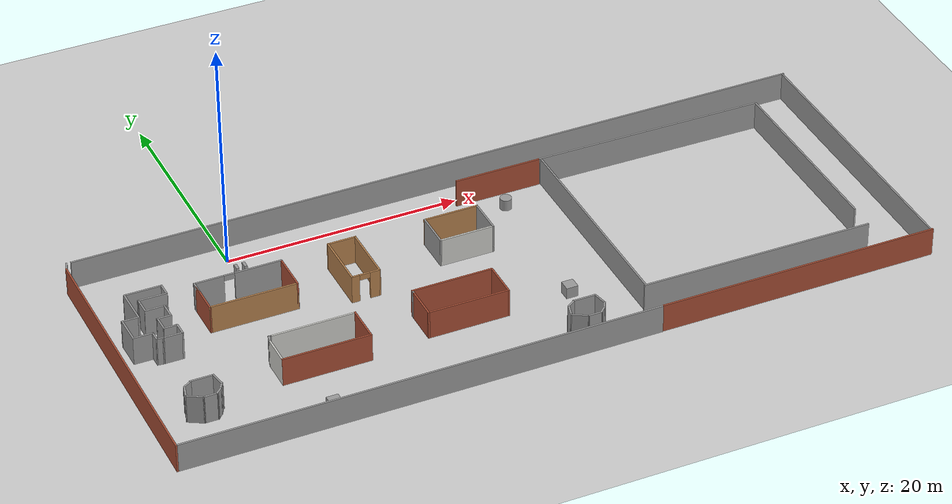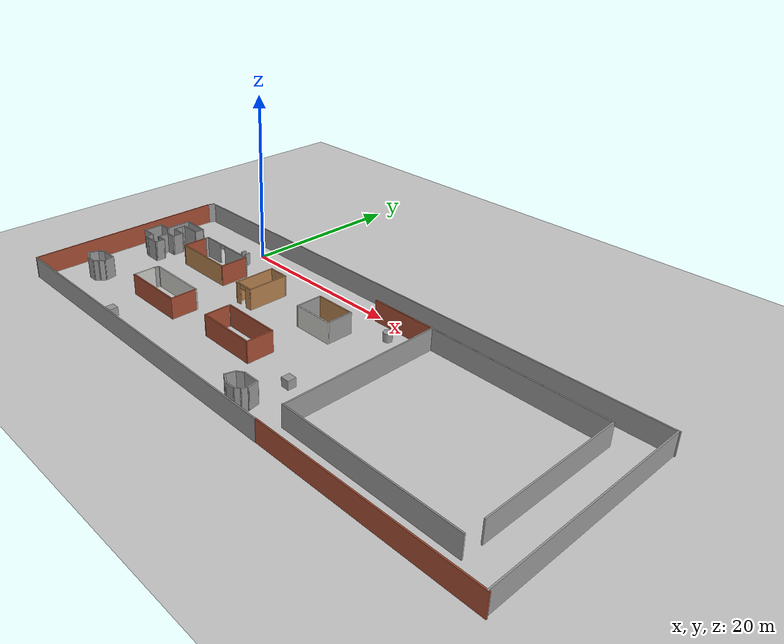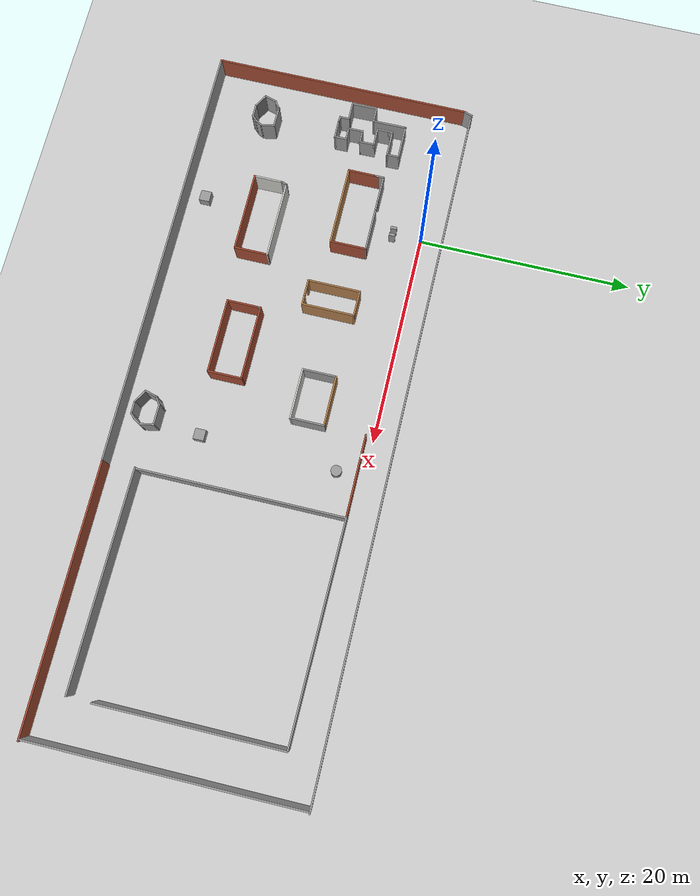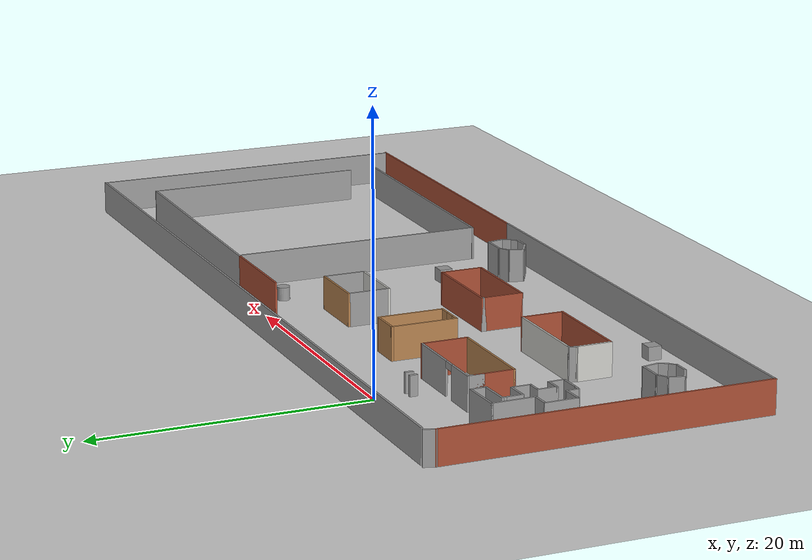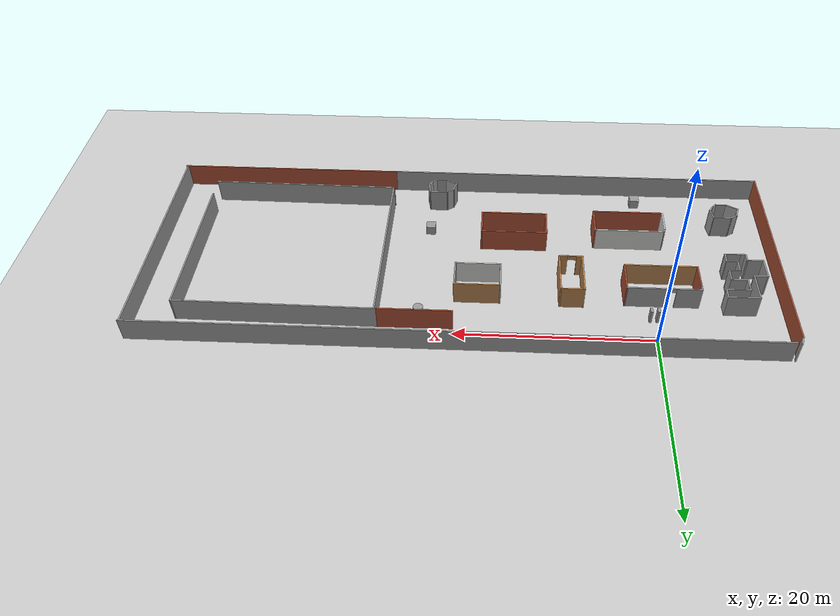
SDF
<sdf version="1.7">
 <world name="default">
  <light name="sun" type="directional">
   <pose>0 0 10 0 -0 0</pose>
   <diffuse>0.8 0.8 0.8 1</diffuse>
   <specular>0.2 0.2 0.2 1</specular>
   <attenuation>
    <range>1000</range>
    <constant>0.9</constant>
    <linear>0.01</linear>
    <quadratic>0.001</quadratic>
   </attenuation>
   <direction>-0.5 0.1 -0.9</direction>
   <spot><inner_angle>0</inner_angle><outer_angle>0</outer_angle><falloff>0</falloff></spot>
  </light>
  <model name="ground_plane">
   <static>1</static>
   <link name="link">
    <collision name="collision">
     <geometry><plane><normal>0 0 1</normal><size>150 100</size></plane></geometry>
     <surface>
      <contact><collide_bitmask>65535</collide_bitmask></contact>
      <friction><ode><mu>100</mu><mu2>50</mu2></ode></friction>
     </surface>
    </collision>
    <visual name="visual">
     <cast_shadows>0</cast_shadows>
     <geometry><plane><normal>0 0 1</normal><size>150 100</size></plane></geometry>
     <material>
      <script><uri>file://media/materials/scripts/gazebo.material</uri><name>Gazebo/Grey</name></script>
     </material>
    </visual>
   </link>
  </model>
  <gravity>0 0 -9.8</gravity>
  <magnetic_field>6e-06 2.3e-05 -4.2e-05</magnetic_field>
  <atmosphere type="adiabatic"/>
  <physics type="ode">
   <max_step_size>0.001</max_step_size>
   <real_time_factor>1</real_time_factor>
   <real_time_update_rate>1000</real_time_update_rate>
  </physics>
  <scene><ambient>0.4 0.4 0.4 1</ambient><background>0.7 0.7 0.7 1</background><shadows>1</shadows></scene>
  <spherical_coordinates>
   <surface_model>EARTH_WGS84</surface_model>
   <latitude_deg>0</latitude_deg>
   <longitude_deg>0</longitude_deg>
   <elevation>0</elevation>
   <heading_deg>0</heading_deg>
  </spherical_coordinates>
  <model name="unit_cylinder">
   <link name="link">
    <inertial>
     <mass>1</mass>
     <inertia><ixx>0.145833</ixx><ixy>0</ixy><ixz>0</ixz><iyy>0.145833</iyy><iyz>0</iyz><izz>0.125</izz></inertia>
    </inertial>
    <visual name="visual">
     <geometry><cylinder><radius>0.5</radius><length>1</length></cylinder></geometry>
     <material>
      <script><name>Gazebo/Grey</name><uri>file://media/materials/scripts/gazebo.material</uri></script>
      <shader type="pixel"><normal_map>__default__</normal_map></shader>
      <ambient>0.3 0.3 0.3 1</ambient>
      <diffuse>0.7 0.7 0.7 1</diffuse>
      <specular>0.01 0.01 0.01 1</specular>
      <emissive>0 0 0 1</emissive>
     </material>
    </visual>
    <collision name="collision">
     <geometry><cylinder><radius>1</radius><length>1</length></cylinder></geometry>
     <surface>
      <friction>
       <ode><mu>1</mu><mu2>1</mu2><fdir1>0 0 0</fdir1><slip1>0</slip1><slip2>0</slip2></ode>
       <torsional>
        <coefficient>1</coefficient>
        <patch_radius>0</patch_radius>
        <surface_radius>0</surface_radius>
        <use_patch_radius>1</use_patch_radius>
        <ode><slip>0</slip></ode>
       </torsional>
      </friction>
      <bounce><restitution_coefficient>0</restitution_coefficient><threshold>1e+06</threshold></bounce>
      <contact>
       <collide_without_contact>0</collide_without_contact>
       <collide_without_contact_bitmask>1</collide_without_contact_bitmask>
       <collide_bitmask>1</collide_bitmask>
       <ode>
        <soft_cfm>0</soft_cfm>
        <soft_erp>0.2</soft_erp>
        <kp>1e+13</kp>
        <kd>1</kd>
        <max_vel>0.01</max_vel>
        <min_depth>0</min_depth>
       </ode>
       <bullet>
        <split_impulse>1</split_impulse>
        <split_impulse_penetration_threshold>-0.01</split_impulse_penetration_threshold>
        <soft_cfm>0</soft_cfm>
        <soft_erp>0.2</soft_erp>
        <kp>1e+13</kp>
        <kd>1</kd>
       </bullet>
      </contact>
     </surface>
    </collision>
   </link>
   <link name="link_1">
    <inertial>
     <mass>1</mass>
     <inertia>
      <ixx>0.166667</ixx>
      <ixy>0</ixy>
      <ixz>0</ixz>
      <iyy>0.166667</iyy>
      <iyz>0</iyz>
      <izz>0.166667</izz>
     </inertia>
    </inertial>
    <pose>-0.400023 -12.7768 -0 0 -0 0</pose>
    <visual name="visual">
     <geometry><box><size>1 1 1</size></box></geometry>
     <material>
      <lighting>1</lighting>
      <script><uri>file://media/materials/scripts/gazebo.material</uri><name>Gazebo/Grey</name></script>
      <shader type="pixel"><normal_map>__default__</normal_map></shader>
      <ambient>0.3 0.3 0.3 1</ambient>
      <diffuse>0.7 0.7 0.7 1</diffuse>
      <specular>0.01 0.01 0.01 1</specular>
      <emissive>0 0 0 1</emissive>
     </material>
    </visual>
    <collision name="collision">
     <geometry><box><size>3 3 1</size></box></geometry>
     <surface>
      <friction>
       <ode><mu>1</mu><mu2>1</mu2><fdir1>0 0 0</fdir1><slip1>0</slip1><slip2>0</slip2></ode>
       <torsional>
        <coefficient>1</coefficient>
        <patch_radius>0</patch_radius>
        <surface_radius>0</surface_radius>
        <use_patch_radius>1</use_patch_radius>
        <ode><slip>0</slip></ode>
       </torsional>
      </friction>
      <bounce><restitution_coefficient>0</restitution_coefficient><threshold>1e+06</threshold></bounce>
      <contact>
       <collide_without_contact>0</collide_without_contact>
       <collide_without_contact_bitmask>1</collide_without_contact_bitmask>
       <collide_bitmask>1</collide_bitmask>
       <ode>
        <soft_cfm>0</soft_cfm>
        <soft_erp>0.2</soft_erp>
        <kp>1e+13</kp>
        <kd>1</kd>
        <max_vel>0.01</max_vel>
        <min_depth>0</min_depth>
       </ode>
       <bullet>
        <split_impulse>1</split_impulse>
        <split_impulse_penetration_threshold>-0.01</split_impulse_penetration_threshold>
        <soft_cfm>0</soft_cfm>
        <soft_erp>0.2</soft_erp>
        <kp>1e+13</kp>
        <kd>1</kd>
       </bullet>
      </contact>
     </surface>
    </collision>
   </link>
   <static>0</static>
   <pose>23.3885 -2.61658 0.499994 4e-06 -3e-06 3.9e-05</pose>
  </model>
  <model name="unregular_wall">
   <pose>-8.69678 -16.3277 0 0 -0 0</pose>
   <link name="Wall_0">
    <collision name="Wall_0_Collision">
     <geometry><box><size>1.99003 0.15 2.5</size></box></geometry>
     <pose>0 0 1.25 0 -0 0</pose>
    </collision>
    <visual name="Wall_0_Visual">
     <pose>0 0 1.25 0 -0 0</pose>
     <geometry><box><size>1.99003 0.15 2.5</size></box></geometry>
     <material>
      <script><uri>file://media/materials/scripts/gazebo.material</uri><name>Gazebo/Grey</name></script>
      <ambient>1 1 1 1</ambient>
     </material>
     <meta><layer>0</layer></meta>
    </visual>
    <pose>0.359239 0.205461 0 0 -0 -0.005435</pose>
   </link>
   <link name="Wall_1">
    <collision name="Wall_1_Collision">
     <geometry><box><size>1.37286 0.15 2.5</size></box></geometry>
     <pose>0 0 1.25 0 -0 0</pose>
    </collision>
    <visual name="Wall_1_Visual">
     <pose>0 0 1.25 0 -0 0</pose>
     <geometry><box><size>1.37286 0.15 2.5</size></box></geometry>
     <material>
      <script><uri>file://media/materials/scripts/gazebo.material</uri><name>Gazebo/Grey</name></script>
      <ambient>1 1 1 1</ambient>
     </material>
     <meta><layer>0</layer></meta>
    </visual>
    <pose>1.40424 -0.400057 0 0 -0 -1.38159</pose>
   </link>
   <link name="Wall_2">
    <collision name="Wall_2_Collision">
     <geometry><box><size>0.814319 0.15 2.5</size></box></geometry>
     <pose>0 0 1.25 0 -0 0</pose>
    </collision>
    <visual name="Wall_2_Visual">
     <pose>0 0 1.25 0 -0 0</pose>
     <geometry><box><size>0.814319 0.15 2.5</size></box></geometry>
     <material>
      <script><uri>file://media/materials/scripts/gazebo.material</uri><name>Gazebo/Grey</name></script>
      <ambient>1 1 1 1</ambient>
     </material>
     <meta><layer>0</layer></meta>
    </visual>
    <pose>1.34688 -1.29035 0 0 -0 -2.08149</pose>
   </link>
   <link name="Wall_3">
    <collision name="Wall_3_Collision">
     <geometry><box><size>0.75 0.15 2.5</size></box></geometry>
     <pose>0 0 1.25 0 -0 0</pose>
    </collision>
    <visual name="Wall_3_Visual">
     <pose>0 0 1.25 0 -0 0</pose>
     <geometry><box><size>0.75 0.15 2.5</size></box></geometry>
     <material>
      <script><uri>file://media/materials/scripts/gazebo.material</uri><name>Gazebo/Grey</name></script>
      <ambient>1 1 1 1</ambient>
     </material>
     <meta><layer>0</layer></meta>
    </visual>
    <pose>0.972394 -1.79226 0 0 -0 -2.35619</pose>
   </link>
   <link name="Wall_4">
    <collision name="Wall_4_Collision">
     <geometry><box><size>1.25 0.15 2.5</size></box></geometry>
     <pose>0 0 1.25 0 -0 0</pose>
    </collision>
    <visual name="Wall_4_Visual">
     <pose>0 0 1.25 0 -0 0</pose>
     <geometry><box><size>1.25 0.15 2.5</size></box></geometry>
     <material>
      <script><uri>file://media/materials/scripts/gazebo.material</uri><name>Gazebo/Grey</name></script>
      <ambient>1 1 1 1</ambient>
     </material>
     <meta><layer>0</layer></meta>
    </visual>
    <pose>0.210262 -2.0044 0 0 -0 3.14159</pose>
   </link>
   <link name="Wall_5">
    <collision name="Wall_5_Collision">
     <geometry><box><size>1.5 0.15 2.5</size></box></geometry>
     <pose>0 0 1.25 0 -0 0</pose>
    </collision>
    <visual name="Wall_5_Visual">
     <pose>0 0 1.25 0 -0 0</pose>
     <geometry><box><size>1.5 0.15 2.5</size></box></geometry>
     <material>
      <script><uri>file://media/materials/scripts/gazebo.material</uri><name>Gazebo/Grey</name></script>
      <ambient>1 1 1 1</ambient>
     </material>
     <meta><layer>0</layer></meta>
    </visual>
    <pose>-0.924305 -1.6669 0 0 -0 2.61799</pose>
   </link>
   <link name="Wall_6">
    <collision name="Wall_6_Collision">
     <geometry><box><size>1.25 0.15 2.5</size></box></geometry>
     <pose>0 0 1.25 0 -0 0</pose>
    </collision>
    <visual name="Wall_6_Visual">
     <pose>0 0 1.25 0 -0 0</pose>
     <geometry><box><size>1.25 0.15 2.5</size></box></geometry>
     <material>
      <script><uri>file://media/materials/scripts/gazebo.material</uri><name>Gazebo/Grey</name></script>
      <ambient>1 1 1 1</ambient>
     </material>
     <meta><layer>0</layer></meta>
    </visual>
    <pose>-1.36652 -0.798136 0 0 -0 1.309</pose>
   </link>
   <link name="Wall_7">
    <collision name="Wall_7_Collision">
     <geometry><box><size>0.969686 0.15 2.5</size></box></geometry>
     <pose>0 0 1.25 0 -0 0</pose>
    </collision>
    <visual name="Wall_7_Visual">
     <pose>0 0 1.25 0 -0 0</pose>
     <geometry><box><size>0.969686 0.15 2.5</size></box></geometry>
     <material>
      <script><uri>file://media/materials/scripts/gazebo.material</uri><name>Gazebo/Grey</name></script>
      <ambient>1 1 1 1</ambient>
     </material>
     <meta><layer>0</layer></meta>
    </visual>
    <pose>-0.887466 -0.033208 0 0 -0 0.606679</pose>
   </link>
   <static>1</static>
  </model>
  <model name="mountan_like">
   <pose>-9.16752 -7.04341 -1e-06 0.014915 -0.000101 1.5834</pose>
   <link name="Wall_0">
    <collision name="Wall_0_Collision">
     <geometry><box><size>1.75 0.15 2.5</size></box></geometry>
     <pose>0 0 1.25 0 -0 0</pose>
    </collision>
    <visual name="Wall_0_Visual">
     <pose>0 0 1.25 0 -0 0</pose>
     <geometry><box><size>1.75 0.15 2.5</size></box></geometry>
     <material>
      <script><uri>file://media/materials/scripts/gazebo.material</uri><name>Gazebo/Grey</name></script>
      <ambient>1 1 1 1</ambient>
     </material>
     <meta><layer>0</layer></meta>
    </visual>
    <pose>-3.17145 -0.675 0 0 -0 -1.5708</pose>
   </link>
   <link name="Wall_1">
    <collision name="Wall_1_Collision">
     <geometry><box><size>1.25 0.15 2.5</size></box></geometry>
     <pose>0 0 1.25 0 -0 0</pose>
    </collision>
    <visual name="Wall_1_Visual">
     <pose>0 0 1.25 0 -0 0</pose>
     <geometry><box><size>1.25 0.15 2.5</size></box></geometry>
     <material>
      <script><uri>file://media/materials/scripts/gazebo.material</uri><name>Gazebo/Grey</name></script>
      <ambient>1 1 1 1</ambient>
     </material>
     <meta><layer>0</layer></meta>
    </visual>
    <pose>-2.62146 -1.475 0 0 -0 0</pose>
   </link>
   <link name="Wall_10">
    <collision name="Wall_10_Collision">
     <geometry><box><size>1.25 0.15 2.5</size></box></geometry>
     <pose>0 0 1.25 0 -0 0</pose>
    </collision>
    <visual name="Wall_10_Visual">
     <pose>0 0 1.25 0 -0 0</pose>
     <geometry><box><size>1.25 0.15 2.5</size></box></geometry>
     <material>
      <script><uri>file://media/materials/scripts/gazebo.material</uri><name>Gazebo/Grey</name></script>
      <ambient>1 1 1 1</ambient>
     </material>
     <meta><layer>0</layer></meta>
    </visual>
    <pose>2.62854 -2.225 0 0 -0 0</pose>
   </link>
   <link name="Wall_11">
    <collision name="Wall_11_Collision">
     <geometry><box><size>3.25 0.15 2.5</size></box></geometry>
     <pose>0 0 1.25 0 -0 0</pose>
    </collision>
    <visual name="Wall_11_Visual">
     <pose>0 0 1.25 0 -0 0</pose>
     <geometry><box><size>3.25 0.15 2.5</size></box></geometry>
     <material>
      <script><uri>file://media/materials/scripts/gazebo.material</uri><name>Gazebo/Grey</name></script>
      <ambient>1 1 1 1</ambient>
     </material>
     <meta><layer>0</layer></meta>
    </visual>
    <pose>3.17855 -0.675 0 0 -0 1.5708</pose>
   </link>
   <link name="Wall_12">
    <collision name="Wall_12_Collision">
     <geometry><box><size>3.25 0.15 2.5</size></box></geometry>
     <pose>0 0 1.25 0 -0 0</pose>
    </collision>
    <visual name="Wall_12_Visual">
     <pose>0 0 1.25 0 -0 0</pose>
     <geometry><box><size>3.25 0.15 2.5</size></box></geometry>
     <material>
      <script><uri>file://media/materials/scripts/gazebo.material</uri><name>Gazebo/Grey</name></script>
      <ambient>1 1 1 1</ambient>
     </material>
     <meta><layer>0</layer></meta>
    </visual>
    <pose>1.62854 0.875 0 0 -0 3.14159</pose>
   </link>
   <link name="Wall_15">
    <collision name="Wall_15_Collision">
     <geometry><box><size>1.5 0.15 2.5</size></box></geometry>
     <pose>0 0 1.25 0 -0 0</pose>
    </collision>
    <visual name="Wall_15_Visual">
     <pose>0 0 1.25 0 -0 0</pose>
     <geometry><box><size>1.5 0.15 2.5</size></box></geometry>
     <material>
      <script><uri>file://media/materials/scripts/gazebo.material</uri><name>Gazebo/Grey</name></script>
      <ambient>1 1 1 1</ambient>
     </material>
     <meta><layer>0</layer></meta>
    </visual>
    <pose>0.078545 1.55 0 0 -0 1.5708</pose>
   </link>
   <link name="Wall_16">
    <collision name="Wall_16_Collision">
     <geometry><box><size>2.5 0.15 2.5</size></box></geometry>
     <pose>0 0 1.25 0 -0 0</pose>
    </collision>
    <visual name="Wall_16_Visual">
     <pose>0 0 1.25 0 -0 0</pose>
     <geometry><box><size>2.5 0.15 2.5</size></box></geometry>
     <material>
      <script><uri>file://media/materials/scripts/gazebo.material</uri><name>Gazebo/Grey</name></script>
      <ambient>1 1 1 1</ambient>
     </material>
     <meta><layer>0</layer></meta>
    </visual>
    <pose>-1.09645 2.225 0 0 -0 3.14159</pose>
   </link>
   <link name="Wall_17">
    <collision name="Wall_17_Collision">
     <geometry><box><size>1.75 0.15 2.5</size></box></geometry>
     <pose>0 0 1.25 0 -0 0</pose>
    </collision>
    <visual name="Wall_17_Visual">
     <pose>0 0 1.25 0 -0 0</pose>
     <geometry><box><size>1.75 0.15 2.5</size></box></geometry>
     <material>
      <script><uri>file://media/materials/scripts/gazebo.material</uri><name>Gazebo/Grey</name></script>
      <ambient>1 1 1 1</ambient>
     </material>
     <meta><layer>0</layer></meta>
    </visual>
    <pose>-2.27146 1.425 0 0 -0 -1.5708</pose>
   </link>
   <link name="Wall_18">
    <collision name="Wall_18_Collision">
     <geometry><box><size>1 0.15 2.5</size></box></geometry>
     <pose>0 0 1.25 0 -0 0</pose>
    </collision>
    <visual name="Wall_18_Visual">
     <pose>0 0 1.25 0 -0 0</pose>
     <geometry><box><size>1 0.15 2.5</size></box></geometry>
     <material>
      <script><uri>file://media/materials/scripts/gazebo.material</uri><name>Gazebo/Grey</name></script>
      <ambient>1 1 1 1</ambient>
     </material>
     <meta><layer>0</layer></meta>
    </visual>
    <pose>-2.69645 0.625 0 0 -0 3.14159</pose>
   </link>
   <link name="Wall_2">
    <collision name="Wall_2_Collision">
     <geometry><box><size>1.25 0.15 2.5</size></box></geometry>
     <pose>0 0 1.25 0 -0 0</pose>
    </collision>
    <visual name="Wall_2_Visual">
     <pose>0 0 1.25 0 -0 0</pose>
     <geometry><box><size>1.25 0.15 2.5</size></box></geometry>
     <material>
      <script><uri>file://media/materials/scripts/gazebo.material</uri><name>Gazebo/Grey</name></script>
      <ambient>1 1 1 1</ambient>
     </material>
     <meta><layer>0</layer></meta>
    </visual>
    <pose>-2.07145 -0.925 0 0 -0 1.5708</pose>
   </link>
   <link name="Wall_20">
    <collision name="Wall_20_Collision">
     <geometry><box><size>0.652494 0.15 2.5</size></box></geometry>
     <pose>0 0 1.25 0 -0 0</pose>
    </collision>
    <visual name="Wall_20_Visual">
     <pose>0 0 1.25 0 -0 0</pose>
     <geometry><box><size>0.652494 0.15 2.5</size></box></geometry>
     <material>
      <script><uri>file://media/materials/scripts/gazebo.material</uri><name>Gazebo/Grey</name></script>
      <ambient>1 1 1 1</ambient>
     </material>
     <meta><layer>0</layer></meta>
    </visual>
    <pose>-3.14646 0.375 0 0 -0 1.47113</pose>
   </link>
   <link name="Wall_3">
    <collision name="Wall_3_Collision">
     <geometry><box><size>1.5 0.15 2.5</size></box></geometry>
     <pose>0 0 1.25 0 -0 0</pose>
    </collision>
    <visual name="Wall_3_Visual">
     <pose>0 0 1.25 0 -0 0</pose>
     <geometry><box><size>1.5 0.15 2.5</size></box></geometry>
     <material>
      <script><uri>file://media/materials/scripts/gazebo.material</uri><name>Gazebo/Grey</name></script>
      <ambient>1 1 1 1</ambient>
     </material>
     <meta><layer>0</layer></meta>
    </visual>
    <pose>-1.39646 -0.375 0 0 -0 0</pose>
   </link>
   <link name="Wall_4">
    <collision name="Wall_4_Collision">
     <geometry><box><size>1.25 0.15 2.5</size></box></geometry>
     <pose>0 0 1.25 0 -0 0</pose>
    </collision>
    <visual name="Wall_4_Visual">
     <pose>0 0 1.25 0 -0 0</pose>
     <geometry><box><size>1.25 0.15 2.5</size></box></geometry>
     <material>
      <script><uri>file://media/materials/scripts/gazebo.material</uri><name>Gazebo/Grey</name></script>
      <ambient>1 1 1 1</ambient>
     </material>
     <meta><layer>0</layer></meta>
    </visual>
    <pose>-0.721455 -0.925 0 0 -0 -1.5708</pose>
   </link>
   <link name="Wall_5">
    <collision name="Wall_5_Collision">
     <geometry><box><size>1.5 0.15 2.5</size></box></geometry>
     <pose>0 0 1.25 0 -0 0</pose>
    </collision>
    <visual name="Wall_5_Visual">
     <pose>0 0 1.25 0 -0 0</pose>
     <geometry><box><size>1.5 0.15 2.5</size></box></geometry>
     <material>
      <script><uri>file://media/materials/scripts/gazebo.material</uri><name>Gazebo/Grey</name></script>
      <ambient>1 1 1 1</ambient>
     </material>
     <meta><layer>0</layer></meta>
    </visual>
    <pose>-0.046455 -1.475 0 0 -0 0</pose>
   </link>
   <link name="Wall_6">
    <collision name="Wall_6_Collision">
     <geometry><box><size>1.75 0.15 2.5</size></box></geometry>
     <pose>0 0 1.25 0 -0 0</pose>
    </collision>
    <visual name="Wall_6_Visual">
     <pose>0 0 1.25 0 -0 0</pose>
     <geometry><box><size>1.75 0.15 2.5</size></box></geometry>
     <material>
      <script><uri>file://media/materials/scripts/gazebo.material</uri><name>Gazebo/Grey</name></script>
      <ambient>1 1 1 1</ambient>
     </material>
     <meta><layer>0</layer></meta>
    </visual>
    <pose>0.628545 -0.675 0 0 -0 1.5708</pose>
   </link>
   <link name="Wall_7">
    <collision name="Wall_7_Collision">
     <geometry><box><size>1.25 0.15 2.5</size></box></geometry>
     <pose>0 0 1.25 0 -0 0</pose>
    </collision>
    <visual name="Wall_7_Visual">
     <pose>0 0 1.25 0 -0 0</pose>
     <geometry><box><size>1.25 0.15 2.5</size></box></geometry>
     <material>
      <script><uri>file://media/materials/scripts/gazebo.material</uri><name>Gazebo/Grey</name></script>
      <ambient>1 1 1 1</ambient>
     </material>
     <meta><layer>0</layer></meta>
    </visual>
    <pose>1.17854 0.125 0 0 -0 0</pose>
   </link>
   <link name="Wall_8">
    <collision name="Wall_8_Collision">
     <geometry><box><size>0.5 0.15 2.5</size></box></geometry>
     <pose>0 0 1.25 0 -0 0</pose>
    </collision>
    <visual name="Wall_8_Visual">
     <pose>0 0 1.25 0 -0 0</pose>
     <geometry><box><size>0.5 0.15 2.5</size></box></geometry>
     <material>
      <script><uri>file://media/materials/scripts/gazebo.material</uri><name>Gazebo/Grey</name></script>
      <ambient>1 1 1 1</ambient>
     </material>
     <meta><layer>0</layer></meta>
    </visual>
    <pose>1.90355 0.125 0 0 -0 0</pose>
   </link>
   <link name="Wall_9">
    <collision name="Wall_9_Collision">
     <geometry><box><size>2.5 0.15 2.5</size></box></geometry>
     <pose>0 0 1.25 0 -0 0</pose>
    </collision>
    <visual name="Wall_9_Visual">
     <pose>0 0 1.25 0 -0 0</pose>
     <geometry><box><size>2.5 0.15 2.5</size></box></geometry>
     <material>
      <script><uri>file://media/materials/scripts/gazebo.material</uri><name>Gazebo/Grey</name></script>
      <ambient>1 1 1 1</ambient>
     </material>
     <meta><layer>0</layer></meta>
    </visual>
    <pose>2.07855 -1.05 0 0 -0 -1.5708</pose>
   </link>
   <static>1</static>
  </model>
  <model name="unregular_wall_0">
   <pose>22 -19.4926 0 0 -0 0</pose>
   <link name="Wall_0">
    <collision name="Wall_0_Collision">
     <geometry><box><size>1.99003 0.15 2.5</size></box></geometry>
     <pose>0 0 1.25 0 -0 0</pose>
    </collision>
    <visual name="Wall_0_Visual">
     <pose>0 0 1.25 0 -0 0</pose>
     <geometry><box><size>1.99003 0.15 2.5</size></box></geometry>
     <material>
      <script><uri>file://media/materials/scripts/gazebo.material</uri><name>Gazebo/Grey</name></script>
      <ambient>1 1 1 1</ambient>
     </material>
     <meta><layer>0</layer></meta>
    </visual>
    <pose>0.359239 0.205461 0 0 -0 -0.005435</pose>
   </link>
   <link name="Wall_1">
    <collision name="Wall_1_Collision">
     <geometry><box><size>1.37286 0.15 2.5</size></box></geometry>
     <pose>0 0 1.25 0 -0 0</pose>
    </collision>
    <visual name="Wall_1_Visual">
     <pose>0 0 1.25 0 -0 0</pose>
     <geometry><box><size>1.37286 0.15 2.5</size></box></geometry>
     <material>
      <script><uri>file://media/materials/scripts/gazebo.material</uri><name>Gazebo/Grey</name></script>
      <ambient>1 1 1 1</ambient>
     </material>
     <meta><layer>0</layer></meta>
    </visual>
    <pose>1.40424 -0.400057 0 0 -0 -1.38159</pose>
   </link>
   <link name="Wall_2">
    <collision name="Wall_2_Collision">
     <geometry><box><size>0.814319 0.15 2.5</size></box></geometry>
     <pose>0 0 1.25 0 -0 0</pose>
    </collision>
    <visual name="Wall_2_Visual">
     <pose>0 0 1.25 0 -0 0</pose>
     <geometry><box><size>0.814319 0.15 2.5</size></box></geometry>
     <material>
      <script><uri>file://media/materials/scripts/gazebo.material</uri><name>Gazebo/Grey</name></script>
      <ambient>1 1 1 1</ambient>
     </material>
     <meta><layer>0</layer></meta>
    </visual>
    <pose>1.34688 -1.29035 0 0 -0 -2.08149</pose>
   </link>
   <link name="Wall_3">
    <collision name="Wall_3_Collision">
     <geometry><box><size>0.75 0.15 2.5</size></box></geometry>
     <pose>0 0 1.25 0 -0 0</pose>
    </collision>
    <visual name="Wall_3_Visual">
     <pose>0 0 1.25 0 -0 0</pose>
     <geometry><box><size>0.75 0.15 2.5</size></box></geometry>
     <material>
      <script><uri>file://media/materials/scripts/gazebo.material</uri><name>Gazebo/Grey</name></script>
      <ambient>1 1 1 1</ambient>
     </material>
     <meta><layer>0</layer></meta>
    </visual>
    <pose>0.972394 -1.79226 0 0 -0 -2.35619</pose>
   </link>
   <link name="Wall_4">
    <collision name="Wall_4_Collision">
     <geometry><box><size>1.25 0.15 2.5</size></box></geometry>
     <pose>0 0 1.25 0 -0 0</pose>
    </collision>
    <visual name="Wall_4_Visual">
     <pose>0 0 1.25 0 -0 0</pose>
     <geometry><box><size>1.25 0.15 2.5</size></box></geometry>
     <material>
      <script><uri>file://media/materials/scripts/gazebo.material</uri><name>Gazebo/Grey</name></script>
      <ambient>1 1 1 1</ambient>
     </material>
     <meta><layer>0</layer></meta>
    </visual>
    <pose>0.210262 -2.0044 0 0 -0 3.14159</pose>
   </link>
   <link name="Wall_5">
    <collision name="Wall_5_Collision">
     <geometry><box><size>1.5 0.15 2.5</size></box></geometry>
     <pose>0 0 1.25 0 -0 0</pose>
    </collision>
    <visual name="Wall_5_Visual">
     <pose>0 0 1.25 0 -0 0</pose>
     <geometry><box><size>1.5 0.15 2.5</size></box></geometry>
     <material>
      <script><uri>file://media/materials/scripts/gazebo.material</uri><name>Gazebo/Grey</name></script>
      <ambient>1 1 1 1</ambient>
     </material>
     <meta><layer>0</layer></meta>
    </visual>
    <pose>-0.924305 -1.6669 0 0 -0 2.61799</pose>
   </link>
   <link name="Wall_6">
    <collision name="Wall_6_Collision">
     <geometry><box><size>1.25 0.15 2.5</size></box></geometry>
     <pose>0 0 1.25 0 -0 0</pose>
    </collision>
    <visual name="Wall_6_Visual">
     <pose>0 0 1.25 0 -0 0</pose>
     <geometry><box><size>1.25 0.15 2.5</size></box></geometry>
     <material>
      <script><uri>file://media/materials/scripts/gazebo.material</uri><name>Gazebo/Grey</name></script>
      <ambient>1 1 1 1</ambient>
     </material>
     <meta><layer>0</layer></meta>
    </visual>
    <pose>-1.36652 -0.798136 0 0 -0 1.309</pose>
   </link>
   <link name="Wall_7">
    <collision name="Wall_7_Collision">
     <geometry><box><size>0.969686 0.15 2.5</size></box></geometry>
     <pose>0 0 1.25 0 -0 0</pose>
    </collision>
    <visual name="Wall_7_Visual">
     <pose>0 0 1.25 0 -0 0</pose>
     <geometry><box><size>0.969686 0.15 2.5</size></box></geometry>
     <material>
      <script><uri>file://media/materials/scripts/gazebo.material</uri><name>Gazebo/Grey</name></script>
      <ambient>1 1 1 1</ambient>
     </material>
     <meta><layer>0</layer></meta>
    </visual>
    <pose>-0.887466 -0.033208 0 0 -0 0.606679</pose>
   </link>
   <static>1</static>
  </model>
  <model name="unit_box">
   <pose>0.471192 -21 0.499995 0 1e-05 0</pose>
   <link name="link">
    <inertial>
     <mass>1</mass>
     <inertia>
      <ixx>0.166667</ixx>
      <ixy>0</ixy>
      <ixz>0</ixz>
      <iyy>0.166667</iyy>
      <iyz>0</iyz>
      <izz>0.166667</izz>
     </inertia>
    </inertial>
    <collision name="collision"><geometry><box><size>1 1 1</size></box></geometry></collision>
    <visual name="visual">
     <geometry><box><size>1 1 1</size></box></geometry>
     <material>
      <script><name>Gazebo/Grey</name><uri>file://media/materials/scripts/gazebo.material</uri></script>
     </material>
    </visual>
   </link>
  </model>
  <audio><device>default</device></audio>
  <model name="narrowgap">
   <link name="Wall_6">
    <pose>1.3 0.7 0.75 0 -0 1.57</pose>
    <inertial>
     <mass>9.375</mass>
     <inertia>
      <ixx>4.90039</ixx>
      <ixy>0</ixy>
      <ixz>0</ixz>
      <iyy>4.93164</iyy>
      <iyz>0</iyz>
      <izz>0.0664062</izz>
     </inertia>
    </inertial>
    <visual name="Wall_6_Visual">
     <geometry><box><size>0.25 0.6 1.5</size></box></geometry>
     <material>
      <script><uri>file://media/materials/scripts/gazebo.material</uri><name>Gazebo/Grey</name></script>
      <ambient>1 1 1 1</ambient>
      <shader type="pixel"><normal_map>__default__</normal_map></shader>
      <diffuse>0.7 0.7 0.7 1</diffuse>
      <specular>0.01 0.01 0.01 1</specular>
      <emissive>0 0 0 1</emissive>
     </material>
     <meta><layer>0</layer></meta>
    </visual>
    <collision name="Wall_6_Collision">
     <geometry><box><size>0.25 0.6 1.5</size></box></geometry>
     <surface>
      <friction>
       <ode><mu>1</mu><mu2>1</mu2><fdir1>0 0 0</fdir1><slip1>0</slip1><slip2>0</slip2></ode>
       <torsional>
        <coefficient>1</coefficient>
        <patch_radius>0</patch_radius>
        <surface_radius>0</surface_radius>
        <use_patch_radius>1</use_patch_radius>
        <ode><slip>0</slip></ode>
       </torsional>
      </friction>
      <bounce><restitution_coefficient>0</restitution_coefficient><threshold>1e+06</threshold></bounce>
      <contact>
       <collide_without_contact>0</collide_without_contact>
       <collide_without_contact_bitmask>1</collide_without_contact_bitmask>
       <collide_bitmask>1</collide_bitmask>
       <ode>
        <soft_cfm>0</soft_cfm>
        <soft_erp>0.2</soft_erp>
        <kp>1e+13</kp>
        <kd>1</kd>
        <max_vel>0.01</max_vel>
        <min_depth>0</min_depth>
       </ode>
       <bullet>
        <split_impulse>1</split_impulse>
        <split_impulse_penetration_threshold>-0.01</split_impulse_penetration_threshold>
        <soft_cfm>0</soft_cfm>
        <soft_erp>0.2</soft_erp>
        <kp>1e+13</kp>
        <kd>1</kd>
       </bullet>
      </contact>
     </surface>
    </collision>
   </link>
   <link name="Wall_7">
    <pose>1.3 0 0.75 0 -0 1.57</pose>
    <inertial>
     <mass>9.375</mass>
     <inertia>
      <ixx>4.90039</ixx>
      <ixy>0</ixy>
      <ixz>0</ixz>
      <iyy>4.93164</iyy>
      <iyz>0</iyz>
      <izz>0.0664062</izz>
     </inertia>
    </inertial>
    <visual name="Wall_7_Visual">
     <geometry><box><size>0.25 0.6 1.5</size></box></geometry>
     <material>
      <script><uri>file://media/materials/scripts/gazebo.material</uri><name>Gazebo/Grey</name></script>
      <ambient>1 1 1 1</ambient>
      <shader type="pixel"><normal_map>__default__</normal_map></shader>
      <diffuse>0.7 0.7 0.7 1</diffuse>
      <specular>0.01 0.01 0.01 1</specular>
      <emissive>0 0 0 1</emissive>
     </material>
     <meta><layer>0</layer></meta>
    </visual>
    <collision name="Wall_7_Collision">
     <geometry><box><size>0.25 0.6 1.5</size></box></geometry>
     <surface>
      <friction>
       <ode><mu>1</mu><mu2>1</mu2><fdir1>0 0 0</fdir1><slip1>0</slip1><slip2>0</slip2></ode>
       <torsional>
        <coefficient>1</coefficient>
        <patch_radius>0</patch_radius>
        <surface_radius>0</surface_radius>
        <use_patch_radius>1</use_patch_radius>
        <ode><slip>0</slip></ode>
       </torsional>
      </friction>
      <bounce><restitution_coefficient>0</restitution_coefficient><threshold>1e+06</threshold></bounce>
      <contact>
       <collide_without_contact>0</collide_without_contact>
       <collide_without_contact_bitmask>1</collide_without_contact_bitmask>
       <collide_bitmask>1</collide_bitmask>
       <ode>
        <soft_cfm>0</soft_cfm>
        <soft_erp>0.2</soft_erp>
        <kp>1e+13</kp>
        <kd>1</kd>
        <max_vel>0.01</max_vel>
        <min_depth>0</min_depth>
       </ode>
       <bullet>
        <split_impulse>1</split_impulse>
        <split_impulse_penetration_threshold>-0.01</split_impulse_penetration_threshold>
        <soft_cfm>0</soft_cfm>
        <soft_erp>0.2</soft_erp>
        <kp>1e+13</kp>
        <kd>1</kd>
       </bullet>
      </contact>
     </surface>
    </collision>
   </link>
   <static>1</static>
   <pose>0.475672 -4.02864 0 0 -0 1.58428</pose>
  </model>
  <model name="slam_world_test.world">
   <link name="Wall_0">
    <pose>0.980896 1.21795 0 0 -0 0</pose>
    <visual name="Wall_0_Visual_2">
     <pose>-0.112099 0 2.25 0 -0 0</pose>
     <geometry><box><size>0.9 0.15 0.5</size></box></geometry>
     <material>
      <script><uri>file://media/materials/scripts/gazebo.material</uri><name>Gazebo/Wood</name></script>
      <ambient>1 1 1 1</ambient>
      <shader type="pixel"/>
     </material>
     <meta><layer>0</layer></meta>
    </visual>
    <visual name="Wall_0_Visual_1">
     <pose>0.79395 0 1.25 0 -0 0</pose>
     <geometry><box><size>0.912099 0.15 2.5</size></box></geometry>
     <material>
      <script><uri>file://media/materials/scripts/gazebo.material</uri><name>Gazebo/Wood</name></script>
      <ambient>1 1 1 1</ambient>
      <shader type="pixel"/>
     </material>
     <meta><layer>0</layer></meta>
    </visual>
    <visual name="Wall_0_Visual_0">
     <pose>-0.90605 0 1.25 0 -0 0</pose>
     <geometry><box><size>0.687901 0.15 2.5</size></box></geometry>
     <material>
      <script><uri>file://media/materials/scripts/gazebo.material</uri><name>Gazebo/Wood</name></script>
      <ambient>1 1 1 1</ambient>
      <shader type="pixel"/>
     </material>
     <meta><layer>0</layer></meta>
    </visual>
    <collision name="Wall_0_Collision_2">
     <pose>-0.112099 0 2.25 0 -0 0</pose>
     <geometry><box><size>0.9 0.15 0.5</size></box></geometry>
     <surface>
      <friction>
       <ode><mu>1</mu><mu2>1</mu2><fdir1>0 0 0</fdir1><slip1>0</slip1><slip2>0</slip2></ode>
       <torsional>
        <coefficient>1</coefficient>
        <patch_radius>0</patch_radius>
        <surface_radius>0</surface_radius>
        <use_patch_radius>1</use_patch_radius>
        <ode><slip>0</slip></ode>
       </torsional>
      </friction>
      <bounce><restitution_coefficient>0</restitution_coefficient><threshold>1e+06</threshold></bounce>
      <contact>
       <collide_without_contact>0</collide_without_contact>
       <collide_without_contact_bitmask>1</collide_without_contact_bitmask>
       <collide_bitmask>1</collide_bitmask>
       <ode>
        <soft_cfm>0</soft_cfm>
        <soft_erp>0.2</soft_erp>
        <kp>1e+13</kp>
        <kd>1</kd>
        <max_vel>0.01</max_vel>
        <min_depth>0</min_depth>
       </ode>
       <bullet>
        <split_impulse>1</split_impulse>
        <split_impulse_penetration_threshold>-0.01</split_impulse_penetration_threshold>
        <soft_cfm>0</soft_cfm>
        <soft_erp>0.2</soft_erp>
        <kp>1e+13</kp>
        <kd>1</kd>
       </bullet>
      </contact>
     </surface>
    </collision>
    <collision name="Wall_0_Collision_0">
     <pose>-0.90605 0 1.25 0 -0 0</pose>
     <geometry><box><size>0.687901 0.15 2.5</size></box></geometry>
     <surface>
      <friction>
       <ode><mu>1</mu><mu2>1</mu2><fdir1>0 0 0</fdir1><slip1>0</slip1><slip2>0</slip2></ode>
       <torsional>
        <coefficient>1</coefficient>
        <patch_radius>0</patch_radius>
        <surface_radius>0</surface_radius>
        <use_patch_radius>1</use_patch_radius>
        <ode><slip>0</slip></ode>
       </torsional>
      </friction>
      <bounce><restitution_coefficient>0</restitution_coefficient><threshold>1e+06</threshold></bounce>
      <contact>
       <collide_without_contact>0</collide_without_contact>
       <collide_without_contact_bitmask>1</collide_without_contact_bitmask>
       <collide_bitmask>1</collide_bitmask>
       <ode>
        <soft_cfm>0</soft_cfm>
        <soft_erp>0.2</soft_erp>
        <kp>1e+13</kp>
        <kd>1</kd>
        <max_vel>0.01</max_vel>
        <min_depth>0</min_depth>
       </ode>
       <bullet>
        <split_impulse>1</split_impulse>
        <split_impulse_penetration_threshold>-0.01</split_impulse_penetration_threshold>
        <soft_cfm>0</soft_cfm>
        <soft_erp>0.2</soft_erp>
        <kp>1e+13</kp>
        <kd>1</kd>
       </bullet>
      </contact>
     </surface>
    </collision>
    <collision name="Wall_0_Collision_1">
     <pose>0.79395 0 1.25 0 -0 0</pose>
     <geometry><box><size>0.912099 0.15 2.5</size></box></geometry>
     <surface>
      <friction>
       <ode><mu>1</mu><mu2>1</mu2><fdir1>0 0 0</fdir1><slip1>0</slip1><slip2>0</slip2></ode>
       <torsional>
        <coefficient>1</coefficient>
        <patch_radius>0</patch_radius>
        <surface_radius>0</surface_radius>
        <use_patch_radius>1</use_patch_radius>
        <ode><slip>0</slip></ode>
       </torsional>
      </friction>
      <bounce><restitution_coefficient>0</restitution_coefficient><threshold>1e+06</threshold></bounce>
      <contact>
       <collide_without_contact>0</collide_without_contact>
       <collide_without_contact_bitmask>1</collide_without_contact_bitmask>
       <collide_bitmask>1</collide_bitmask>
       <ode>
        <soft_cfm>0</soft_cfm>
        <soft_erp>0.2</soft_erp>
        <kp>1e+13</kp>
        <kd>1</kd>
        <max_vel>0.01</max_vel>
        <min_depth>0</min_depth>
       </ode>
       <bullet>
        <split_impulse>1</split_impulse>
        <split_impulse_penetration_threshold>-0.01</split_impulse_penetration_threshold>
        <soft_cfm>0</soft_cfm>
        <soft_erp>0.2</soft_erp>
        <kp>1e+13</kp>
        <kd>1</kd>
       </bullet>
      </contact>
     </surface>
    </collision>
   </link>
   <link name="Wall_1">
    <pose>2.1559 3.64295 0 0 -0 1.5708</pose>
    <visual name="Wall_1_Visual">
     <pose>0 0 1.25 0 -0 0</pose>
     <geometry><box><size>5 0.15 2.5</size></box></geometry>
     <material>
      <script><uri>file://media/materials/scripts/gazebo.material</uri><name>Gazebo/Wood</name></script>
      <ambient>1 1 1 1</ambient>
      <shader type="pixel"/>
     </material>
     <meta><layer>0</layer></meta>
    </visual>
    <collision name="Wall_1_Collision">
     <pose>0 0 1.25 0 -0 0</pose>
     <geometry><box><size>5 0.15 2.5</size></box></geometry>
     <surface>
      <friction>
       <ode><mu>1</mu><mu2>1</mu2><fdir1>0 0 0</fdir1><slip1>0</slip1><slip2>0</slip2></ode>
       <torsional>
        <coefficient>1</coefficient>
        <patch_radius>0</patch_radius>
        <surface_radius>0</surface_radius>
        <use_patch_radius>1</use_patch_radius>
        <ode><slip>0</slip></ode>
       </torsional>
      </friction>
      <bounce><restitution_coefficient>0</restitution_coefficient><threshold>1e+06</threshold></bounce>
      <contact>
       <collide_without_contact>0</collide_without_contact>
       <collide_without_contact_bitmask>1</collide_without_contact_bitmask>
       <collide_bitmask>1</collide_bitmask>
       <ode>
        <soft_cfm>0</soft_cfm>
        <soft_erp>0.2</soft_erp>
        <kp>1e+13</kp>
        <kd>1</kd>
        <max_vel>0.01</max_vel>
        <min_depth>0</min_depth>
       </ode>
       <bullet>
        <split_impulse>1</split_impulse>
        <split_impulse_penetration_threshold>-0.01</split_impulse_penetration_threshold>
        <soft_cfm>0</soft_cfm>
        <soft_erp>0.2</soft_erp>
        <kp>1e+13</kp>
        <kd>1</kd>
       </bullet>
      </contact>
     </surface>
    </collision>
   </link>
   <link name="Wall_11">
    <pose>8.13072 4.30392 0 0 -0 1.5708</pose>
    <visual name="Wall_11_Visual">
     <pose>0 0 1.25 0 -0 0</pose>
     <geometry><box><size>3.25 0.15 2.5</size></box></geometry>
     <material>
      <script><uri>file://media/materials/scripts/gazebo.material</uri><name>Gazebo/Grey</name></script>
      <ambient>1 1 1 1</ambient>
      <shader type="pixel"/>
     </material>
     <meta><layer>0</layer></meta>
    </visual>
    <collision name="Wall_11_Collision">
     <pose>0 0 1.25 0 -0 0</pose>
     <geometry><box><size>3.25 0.15 2.5</size></box></geometry>
     <surface>
      <friction>
       <ode><mu>1</mu><mu2>1</mu2><fdir1>0 0 0</fdir1><slip1>0</slip1><slip2>0</slip2></ode>
       <torsional>
        <coefficient>1</coefficient>
        <patch_radius>0</patch_radius>
        <surface_radius>0</surface_radius>
        <use_patch_radius>1</use_patch_radius>
        <ode><slip>0</slip></ode>
       </torsional>
      </friction>
      <bounce><restitution_coefficient>0</restitution_coefficient><threshold>1e+06</threshold></bounce>
      <contact>
       <collide_without_contact>0</collide_without_contact>
       <collide_without_contact_bitmask>1</collide_without_contact_bitmask>
       <collide_bitmask>1</collide_bitmask>
       <ode>
        <soft_cfm>0</soft_cfm>
        <soft_erp>0.2</soft_erp>
        <kp>1e+13</kp>
        <kd>1</kd>
        <max_vel>0.01</max_vel>
        <min_depth>0</min_depth>
       </ode>
       <bullet>
        <split_impulse>1</split_impulse>
        <split_impulse_penetration_threshold>-0.01</split_impulse_penetration_threshold>
        <soft_cfm>0</soft_cfm>
        <soft_erp>0.2</soft_erp>
        <kp>1e+13</kp>
        <kd>1</kd>
       </bullet>
      </contact>
     </surface>
    </collision>
   </link>
   <link name="Wall_12">
    <pose>10.4307 5.85392 0 0 -0 0</pose>
    <visual name="Wall_12_Visual">
     <pose>0 0 1.25 0 -0 0</pose>
     <geometry><box><size>4.75 0.15 2.5</size></box></geometry>
     <material>
      <script><uri>file://media/materials/scripts/gazebo.material</uri><name>Gazebo/Wood</name></script>
      <ambient>1 1 1 1</ambient>
      <shader type="pixel"/>
     </material>
     <meta><layer>0</layer></meta>
    </visual>
    <collision name="Wall_12_Collision">
     <pose>0 0 1.25 0 -0 0</pose>
     <geometry><box><size>4.75 0.15 2.5</size></box></geometry>
     <surface>
      <friction>
       <ode><mu>1</mu><mu2>1</mu2><fdir1>0 0 0</fdir1><slip1>0</slip1><slip2>0</slip2></ode>
       <torsional>
        <coefficient>1</coefficient>
        <patch_radius>0</patch_radius>
        <surface_radius>0</surface_radius>
        <use_patch_radius>1</use_patch_radius>
        <ode><slip>0</slip></ode>
       </torsional>
      </friction>
      <bounce><restitution_coefficient>0</restitution_coefficient><threshold>1e+06</threshold></bounce>
      <contact>
       <collide_without_contact>0</collide_without_contact>
       <collide_without_contact_bitmask>1</collide_without_contact_bitmask>
       <collide_bitmask>1</collide_bitmask>
       <ode>
        <soft_cfm>0</soft_cfm>
        <soft_erp>0.2</soft_erp>
        <kp>1e+13</kp>
        <kd>1</kd>
        <max_vel>0.01</max_vel>
        <min_depth>0</min_depth>
       </ode>
       <bullet>
        <split_impulse>1</split_impulse>
        <split_impulse_penetration_threshold>-0.01</split_impulse_penetration_threshold>
        <soft_cfm>0</soft_cfm>
        <soft_erp>0.2</soft_erp>
        <kp>1e+13</kp>
        <kd>1</kd>
       </bullet>
      </contact>
     </surface>
    </collision>
   </link>
   <link name="Wall_13">
    <pose>12.7307 4.30392 0 0 0 -1.5708</pose>
    <visual name="Wall_13_Visual">
     <pose>0 0 1.25 0 -0 0</pose>
     <geometry><box><size>3.25 0.15 2.5</size></box></geometry>
     <material>
      <script><uri>file://media/materials/scripts/gazebo.material</uri><name>Gazebo/Grey</name></script>
      <ambient>1 1 1 1</ambient>
      <shader type="pixel"/>
     </material>
     <meta><layer>0</layer></meta>
    </visual>
    <collision name="Wall_13_Collision">
     <pose>0 0 1.25 0 -0 0</pose>
     <geometry><box><size>3.25 0.15 2.5</size></box></geometry>
     <surface>
      <friction>
       <ode><mu>1</mu><mu2>1</mu2><fdir1>0 0 0</fdir1><slip1>0</slip1><slip2>0</slip2></ode>
       <torsional>
        <coefficient>1</coefficient>
        <patch_radius>0</patch_radius>
        <surface_radius>0</surface_radius>
        <use_patch_radius>1</use_patch_radius>
        <ode><slip>0</slip></ode>
       </torsional>
      </friction>
      <bounce><restitution_coefficient>0</restitution_coefficient><threshold>1e+06</threshold></bounce>
      <contact>
       <collide_without_contact>0</collide_without_contact>
       <collide_without_contact_bitmask>1</collide_without_contact_bitmask>
       <collide_bitmask>1</collide_bitmask>
       <ode>
        <soft_cfm>0</soft_cfm>
        <soft_erp>0.2</soft_erp>
        <kp>1e+13</kp>
        <kd>1</kd>
        <max_vel>0.01</max_vel>
        <min_depth>0</min_depth>
       </ode>
       <bullet>
        <split_impulse>1</split_impulse>
        <split_impulse_penetration_threshold>-0.01</split_impulse_penetration_threshold>
        <soft_cfm>0</soft_cfm>
        <soft_erp>0.2</soft_erp>
        <kp>1e+13</kp>
        <kd>1</kd>
       </bullet>
      </contact>
     </surface>
    </collision>
   </link>
   <link name="Wall_14">
    <pose>10.4307 2.75392 0 0 -0 3.14159</pose>
    <visual name="Wall_14_Visual">
     <pose>0 0 1.25 0 -0 0</pose>
     <geometry><box><size>4.75 0.15 2.5</size></box></geometry>
     <material>
      <script><uri>file://media/materials/scripts/gazebo.material</uri><name>Gazebo/CeilingTiled</name></script>
      <ambient>1 1 1 1</ambient>
      <shader type="pixel"/>
     </material>
     <meta><layer>0</layer></meta>
    </visual>
    <collision name="Wall_14_Collision">
     <pose>0 0 1.25 0 -0 0</pose>
     <geometry><box><size>4.75 0.15 2.5</size></box></geometry>
     <surface>
      <friction>
       <ode><mu>1</mu><mu2>1</mu2><fdir1>0 0 0</fdir1><slip1>0</slip1><slip2>0</slip2></ode>
       <torsional>
        <coefficient>1</coefficient>
        <patch_radius>0</patch_radius>
        <surface_radius>0</surface_radius>
        <use_patch_radius>1</use_patch_radius>
        <ode><slip>0</slip></ode>
       </torsional>
      </friction>
      <bounce><restitution_coefficient>0</restitution_coefficient><threshold>1e+06</threshold></bounce>
      <contact>
       <collide_without_contact>0</collide_without_contact>
       <collide_without_contact_bitmask>1</collide_without_contact_bitmask>
       <collide_bitmask>1</collide_bitmask>
       <ode>
        <soft_cfm>0</soft_cfm>
        <soft_erp>0.2</soft_erp>
        <kp>1e+13</kp>
        <kd>1</kd>
        <max_vel>0.01</max_vel>
        <min_depth>0</min_depth>
       </ode>
       <bullet>
        <split_impulse>1</split_impulse>
        <split_impulse_penetration_threshold>-0.01</split_impulse_penetration_threshold>
        <soft_cfm>0</soft_cfm>
        <soft_erp>0.2</soft_erp>
        <kp>1e+13</kp>
        <kd>1</kd>
       </bullet>
      </contact>
     </surface>
    </collision>
   </link>
   <link name="Wall_16">
    <pose>-9.1174 -4.89748 0 0 0 -1.5708</pose>
    <visual name="Wall_16_Visual">
     <pose>0 0 1.25 0 -0 0</pose>
     <geometry><box><size>2.75 0.15 2.5</size></box></geometry>
     <material>
      <script><uri>file://media/materials/scripts/gazebo.material</uri><name>Gazebo/CeilingTiled</name></script>
      <ambient>1 1 1 1</ambient>
      <shader type="pixel"/>
     </material>
     <meta><layer>0</layer></meta>
    </visual>
    <collision name="Wall_16_Collision">
     <pose>0 0 1.25 0 -0 0</pose>
     <geometry><box><size>2.75 0.15 2.5</size></box></geometry>
     <surface>
      <friction>
       <ode><mu>1</mu><mu2>1</mu2><fdir1>0 0 0</fdir1><slip1>0</slip1><slip2>0</slip2></ode>
       <torsional>
        <coefficient>1</coefficient>
        <patch_radius>0</patch_radius>
        <surface_radius>0</surface_radius>
        <use_patch_radius>1</use_patch_radius>
        <ode><slip>0</slip></ode>
       </torsional>
      </friction>
      <bounce><restitution_coefficient>0</restitution_coefficient><threshold>1e+06</threshold></bounce>
      <contact>
       <collide_without_contact>0</collide_without_contact>
       <collide_without_contact_bitmask>1</collide_without_contact_bitmask>
       <collide_bitmask>1</collide_bitmask>
       <ode>
        <soft_cfm>0</soft_cfm>
        <soft_erp>0.2</soft_erp>
        <kp>1e+13</kp>
        <kd>1</kd>
        <max_vel>0.01</max_vel>
        <min_depth>0</min_depth>
       </ode>
       <bullet>
        <split_impulse>1</split_impulse>
        <split_impulse_penetration_threshold>-0.01</split_impulse_penetration_threshold>
        <soft_cfm>0</soft_cfm>
        <soft_erp>0.2</soft_erp>
        <kp>1e+13</kp>
        <kd>1</kd>
       </bullet>
      </contact>
     </surface>
    </collision>
   </link>
   <link name="Wall_17">
    <pose>-5.4424 -6.19749 0 0 -0 0</pose>
    <visual name="Wall_17_Visual">
     <pose>0 0 1.25 0 -0 0</pose>
     <geometry><box><size>7.5 0.15 2.5</size></box></geometry>
     <material>
      <script><uri>file://media/materials/scripts/gazebo.material</uri><name>Gazebo/Bricks</name></script>
      <ambient>1 1 1 1</ambient>
      <shader type="pixel"/>
     </material>
     <meta><layer>0</layer></meta>
    </visual>
    <collision name="Wall_17_Collision">
     <pose>0 0 1.25 0 -0 0</pose>
     <geometry><box><size>7.5 0.15 2.5</size></box></geometry>
     <surface>
      <friction>
       <ode><mu>1</mu><mu2>1</mu2><fdir1>0 0 0</fdir1><slip1>0</slip1><slip2>0</slip2></ode>
       <torsional>
        <coefficient>1</coefficient>
        <patch_radius>0</patch_radius>
        <surface_radius>0</surface_radius>
        <use_patch_radius>1</use_patch_radius>
        <ode><slip>0</slip></ode>
       </torsional>
      </friction>
      <bounce><restitution_coefficient>0</restitution_coefficient><threshold>1e+06</threshold></bounce>
      <contact>
       <collide_without_contact>0</collide_without_contact>
       <collide_without_contact_bitmask>1</collide_without_contact_bitmask>
       <collide_bitmask>1</collide_bitmask>
       <ode>
        <soft_cfm>0</soft_cfm>
        <soft_erp>0.2</soft_erp>
        <kp>1e+13</kp>
        <kd>1</kd>
        <max_vel>0.01</max_vel>
        <min_depth>0</min_depth>
       </ode>
       <bullet>
        <split_impulse>1</split_impulse>
        <split_impulse_penetration_threshold>-0.01</split_impulse_penetration_threshold>
        <soft_cfm>0</soft_cfm>
        <soft_erp>0.2</soft_erp>
        <kp>1e+13</kp>
        <kd>1</kd>
       </bullet>
      </contact>
     </surface>
    </collision>
   </link>
   <link name="Wall_17_clone">
    <pose>16.3654 9.67924 0 0 -0 0</pose>
    <inertial>
     <mass>1</mass>
     <inertia><ixx>1</ixx><ixy>0</ixy><ixz>0</ixz><iyy>1</iyy><iyz>0</iyz><izz>1</izz></inertia>
    </inertial>
    <visual name="Wall_17_Visual">
     <pose>0 0 1.25 0 -0 0</pose>
     <geometry><box><size>7.5 0.15 2.5</size></box></geometry>
     <material>
      <script><uri>file://media/materials/scripts/gazebo.material</uri><name>Gazebo/Bricks</name></script>
      <ambient>1 1 1 1</ambient>
      <shader type="pixel"><normal_map>__default__</normal_map></shader>
     </material>
     <meta><layer>0</layer></meta>
    </visual>
    <collision name="Wall_17_Collision">
     <pose>0 0 1.25 0 -0 0</pose>
     <geometry><box><size>7.5 0.15 2.5</size></box></geometry>
     <surface>
      <friction>
       <ode><mu>1</mu><mu2>1</mu2><fdir1>0 0 0</fdir1><slip1>0</slip1><slip2>0</slip2></ode>
       <torsional>
        <coefficient>1</coefficient>
        <patch_radius>0</patch_radius>
        <surface_radius>0</surface_radius>
        <use_patch_radius>1</use_patch_radius>
        <ode><slip>0</slip></ode>
       </torsional>
      </friction>
      <bounce><restitution_coefficient>0</restitution_coefficient><threshold>1e+06</threshold></bounce>
      <contact>
       <collide_without_contact>0</collide_without_contact>
       <collide_without_contact_bitmask>1</collide_without_contact_bitmask>
       <collide_bitmask>1</collide_bitmask>
       <ode>
        <soft_cfm>0</soft_cfm>
        <soft_erp>0.2</soft_erp>
        <kp>1e+13</kp>
        <kd>1</kd>
        <max_vel>0.01</max_vel>
        <min_depth>0</min_depth>
       </ode>
       <bullet>
        <split_impulse>1</split_impulse>
        <split_impulse_penetration_threshold>-0.01</split_impulse_penetration_threshold>
        <soft_cfm>0</soft_cfm>
        <soft_erp>0.2</soft_erp>
        <kp>1e+13</kp>
        <kd>1</kd>
       </bullet>
      </contact>
     </surface>
    </collision>
   </link>
   <link name="Wall_18">
    <pose>-1.7674 -4.64748 0 0 -0 1.5708</pose>
    <visual name="Wall_18_Visual">
     <pose>0 0 1.25 0 -0 0</pose>
     <geometry><box><size>3.25 0.15 2.5</size></box></geometry>
     <material>
      <script><uri>file://media/materials/scripts/gazebo.material</uri><name>Gazebo/Bricks</name></script>
      <ambient>1 1 1 1</ambient>
      <shader type="pixel"/>
     </material>
     <meta><layer>0</layer></meta>
    </visual>
    <collision name="Wall_18_Collision">
     <pose>0 0 1.25 0 -0 0</pose>
     <geometry><box><size>3.25 0.15 2.5</size></box></geometry>
     <surface>
      <friction>
       <ode><mu>1</mu><mu2>1</mu2><fdir1>0 0 0</fdir1><slip1>0</slip1><slip2>0</slip2></ode>
       <torsional>
        <coefficient>1</coefficient>
        <patch_radius>0</patch_radius>
        <surface_radius>0</surface_radius>
        <use_patch_radius>1</use_patch_radius>
        <ode><slip>0</slip></ode>
       </torsional>
      </friction>
      <bounce><restitution_coefficient>0</restitution_coefficient><threshold>1e+06</threshold></bounce>
      <contact>
       <collide_without_contact>0</collide_without_contact>
       <collide_without_contact_bitmask>1</collide_without_contact_bitmask>
       <collide_bitmask>1</collide_bitmask>
       <ode>
        <soft_cfm>0</soft_cfm>
        <soft_erp>0.2</soft_erp>
        <kp>1e+13</kp>
        <kd>1</kd>
        <max_vel>0.01</max_vel>
        <min_depth>0</min_depth>
       </ode>
       <bullet>
        <split_impulse>1</split_impulse>
        <split_impulse_penetration_threshold>-0.01</split_impulse_penetration_threshold>
        <soft_cfm>0</soft_cfm>
        <soft_erp>0.2</soft_erp>
        <kp>1e+13</kp>
        <kd>1</kd>
       </bullet>
      </contact>
     </surface>
    </collision>
   </link>
   <link name="Wall_19">
    <pose>-5.3174 -3.09749 0 0 -0 3.14159</pose>
    <visual name="Wall_19_Visual">
     <pose>0 0 1.25 0 -0 0</pose>
     <geometry><box><size>7.25 0.15 2.5</size></box></geometry>
     <material>
      <script><uri>file://media/materials/scripts/gazebo.material</uri><name>Gazebo/CeilingTiled</name></script>
      <ambient>1 1 1 1</ambient>
      <shader type="pixel"/>
     </material>
     <meta><layer>0</layer></meta>
    </visual>
    <collision name="Wall_19_Collision">
     <pose>0 0 1.25 0 -0 0</pose>
     <geometry><box><size>7.25 0.15 2.5</size></box></geometry>
     <surface>
      <friction>
       <ode><mu>1</mu><mu2>1</mu2><fdir1>0 0 0</fdir1><slip1>0</slip1><slip2>0</slip2></ode>
       <torsional>
        <coefficient>1</coefficient>
        <patch_radius>0</patch_radius>
        <surface_radius>0</surface_radius>
        <use_patch_radius>1</use_patch_radius>
        <ode><slip>0</slip></ode>
       </torsional>
      </friction>
      <bounce><restitution_coefficient>0</restitution_coefficient><threshold>1e+06</threshold></bounce>
      <contact>
       <collide_without_contact>0</collide_without_contact>
       <collide_without_contact_bitmask>1</collide_without_contact_bitmask>
       <collide_bitmask>1</collide_bitmask>
       <ode>
        <soft_cfm>0</soft_cfm>
        <soft_erp>0.2</soft_erp>
        <kp>1e+13</kp>
        <kd>1</kd>
        <max_vel>0.01</max_vel>
        <min_depth>0</min_depth>
       </ode>
       <bullet>
        <split_impulse>1</split_impulse>
        <split_impulse_penetration_threshold>-0.01</split_impulse_penetration_threshold>
        <soft_cfm>0</soft_cfm>
        <soft_erp>0.2</soft_erp>
        <kp>1e+13</kp>
        <kd>1</kd>
       </bullet>
      </contact>
     </surface>
    </collision>
   </link>
   <link name="Wall_2">
    <pose>0.980896 6.06795 0 0 -0 3.14159</pose>
    <visual name="Wall_2_Visual">
     <pose>0 0 1.25 0 -0 0</pose>
     <geometry><box><size>2.5 0.15 2.5</size></box></geometry>
     <material>
      <script><uri>file://media/materials/scripts/gazebo.material</uri><name>Gazebo/Wood</name></script>
      <ambient>1 1 1 1</ambient>
      <shader type="pixel"/>
     </material>
     <meta><layer>0</layer></meta>
    </visual>
    <collision name="Wall_2_Collision">
     <pose>0 0 1.25 0 -0 0</pose>
     <geometry><box><size>2.5 0.15 2.5</size></box></geometry>
     <surface>
      <friction>
       <ode><mu>1</mu><mu2>1</mu2><fdir1>0 0 0</fdir1><slip1>0</slip1><slip2>0</slip2></ode>
       <torsional>
        <coefficient>1</coefficient>
        <patch_radius>0</patch_radius>
        <surface_radius>0</surface_radius>
        <use_patch_radius>1</use_patch_radius>
        <ode><slip>0</slip></ode>
       </torsional>
      </friction>
      <bounce><restitution_coefficient>0</restitution_coefficient><threshold>1e+06</threshold></bounce>
      <contact>
       <collide_without_contact>0</collide_without_contact>
       <collide_without_contact_bitmask>1</collide_without_contact_bitmask>
       <collide_bitmask>1</collide_bitmask>
       <ode>
        <soft_cfm>0</soft_cfm>
        <soft_erp>0.2</soft_erp>
        <kp>1e+13</kp>
        <kd>1</kd>
        <max_vel>0.01</max_vel>
        <min_depth>0</min_depth>
       </ode>
       <bullet>
        <split_impulse>1</split_impulse>
        <split_impulse_penetration_threshold>-0.01</split_impulse_penetration_threshold>
        <soft_cfm>0</soft_cfm>
        <soft_erp>0.2</soft_erp>
        <kp>1e+13</kp>
        <kd>1</kd>
       </bullet>
      </contact>
     </surface>
    </collision>
   </link>
   <link name="Wall_20">
    <pose>-8.9174 -3.09749 0 0 -0 3.14159</pose>
    <visual name="Wall_20_Visual">
     <pose>0 0 1.25 0 -0 0</pose>
     <geometry><box><size>0.25 0.15 2.5</size></box></geometry>
     <material>
      <script><uri>file://media/materials/scripts/gazebo.material</uri><name>Gazebo/Grey</name></script>
      <ambient>1 1 1 1</ambient>
      <shader type="pixel"/>
     </material>
     <meta><layer>0</layer></meta>
    </visual>
    <collision name="Wall_20_Collision">
     <pose>0 0 1.25 0 -0 0</pose>
     <geometry><box><size>0.25 0.15 2.5</size></box></geometry>
     <surface>
      <friction>
       <ode><mu>1</mu><mu2>1</mu2><fdir1>0 0 0</fdir1><slip1>0</slip1><slip2>0</slip2></ode>
       <torsional>
        <coefficient>1</coefficient>
        <patch_radius>0</patch_radius>
        <surface_radius>0</surface_radius>
        <use_patch_radius>1</use_patch_radius>
        <ode><slip>0</slip></ode>
       </torsional>
      </friction>
      <bounce><restitution_coefficient>0</restitution_coefficient><threshold>1e+06</threshold></bounce>
      <contact>
       <collide_without_contact>0</collide_without_contact>
       <collide_without_contact_bitmask>1</collide_without_contact_bitmask>
       <collide_bitmask>1</collide_bitmask>
       <ode>
        <soft_cfm>0</soft_cfm>
        <soft_erp>0.2</soft_erp>
        <kp>1e+13</kp>
        <kd>1</kd>
        <max_vel>0.01</max_vel>
        <min_depth>0</min_depth>
       </ode>
       <bullet>
        <split_impulse>1</split_impulse>
        <split_impulse_penetration_threshold>-0.01</split_impulse_penetration_threshold>
        <soft_cfm>0</soft_cfm>
        <soft_erp>0.2</soft_erp>
        <kp>1e+13</kp>
        <kd>1</kd>
       </bullet>
      </contact>
     </surface>
    </collision>
   </link>
   <link name="Wall_21">
    <pose>-8.9674 -3.09749 0 0 -0 0</pose>
    <visual name="Wall_21_Visual">
     <pose>0 0 1.25 0 -0 0</pose>
     <geometry><box><size>0.15 0.15 2.5</size></box></geometry>
     <material>
      <script><uri>file://media/materials/scripts/gazebo.material</uri><name>Gazebo/Grey</name></script>
      <ambient>1 1 1 1</ambient>
      <shader type="pixel"/>
     </material>
     <meta><layer>0</layer></meta>
    </visual>
    <collision name="Wall_21_Collision">
     <pose>0 0 1.25 0 -0 0</pose>
     <geometry><box><size>0.15 0.15 2.5</size></box></geometry>
     <surface>
      <friction>
       <ode><mu>1</mu><mu2>1</mu2><fdir1>0 0 0</fdir1><slip1>0</slip1><slip2>0</slip2></ode>
       <torsional>
        <coefficient>1</coefficient>
        <patch_radius>0</patch_radius>
        <surface_radius>0</surface_radius>
        <use_patch_radius>1</use_patch_radius>
        <ode><slip>0</slip></ode>
       </torsional>
      </friction>
      <bounce><restitution_coefficient>0</restitution_coefficient><threshold>1e+06</threshold></bounce>
      <contact>
       <collide_without_contact>0</collide_without_contact>
       <collide_without_contact_bitmask>1</collide_without_contact_bitmask>
       <collide_bitmask>1</collide_bitmask>
       <ode>
        <soft_cfm>0</soft_cfm>
        <soft_erp>0.2</soft_erp>
        <kp>1e+13</kp>
        <kd>1</kd>
        <max_vel>0.01</max_vel>
        <min_depth>0</min_depth>
       </ode>
       <bullet>
        <split_impulse>1</split_impulse>
        <split_impulse_penetration_threshold>-0.01</split_impulse_penetration_threshold>
        <soft_cfm>0</soft_cfm>
        <soft_erp>0.2</soft_erp>
        <kp>1e+13</kp>
        <kd>1</kd>
       </bullet>
      </contact>
     </surface>
    </collision>
   </link>
   <link name="Wall_22">
    <pose>-9.0424 -3.34749 0 0 0 -1.86225</pose>
    <visual name="Wall_22_Visual">
     <pose>0 0 1.25 0 -0 0</pose>
     <geometry><box><size>0.672015 0.15 2.5</size></box></geometry>
     <material>
      <script><uri>file://media/materials/scripts/gazebo.material</uri><name>Gazebo/Grey</name></script>
      <ambient>1 1 1 1</ambient>
      <shader type="pixel"/>
     </material>
     <meta><layer>0</layer></meta>
    </visual>
    <collision name="Wall_22_Collision">
     <pose>0 0 1.25 0 -0 0</pose>
     <geometry><box><size>0.672015 0.15 2.5</size></box></geometry>
     <surface>
      <friction>
       <ode><mu>1</mu><mu2>1</mu2><fdir1>0 0 0</fdir1><slip1>0</slip1><slip2>0</slip2></ode>
       <torsional>
        <coefficient>1</coefficient>
        <patch_radius>0</patch_radius>
        <surface_radius>0</surface_radius>
        <use_patch_radius>1</use_patch_radius>
        <ode><slip>0</slip></ode>
       </torsional>
      </friction>
      <bounce><restitution_coefficient>0</restitution_coefficient><threshold>1e+06</threshold></bounce>
      <contact>
       <collide_without_contact>0</collide_without_contact>
       <collide_without_contact_bitmask>1</collide_without_contact_bitmask>
       <collide_bitmask>1</collide_bitmask>
       <ode>
        <soft_cfm>0</soft_cfm>
        <soft_erp>0.2</soft_erp>
        <kp>1e+13</kp>
        <kd>1</kd>
        <max_vel>0.01</max_vel>
        <min_depth>0</min_depth>
       </ode>
       <bullet>
        <split_impulse>1</split_impulse>
        <split_impulse_penetration_threshold>-0.01</split_impulse_penetration_threshold>
        <soft_cfm>0</soft_cfm>
        <soft_erp>0.2</soft_erp>
        <kp>1e+13</kp>
        <kd>1</kd>
       </bullet>
      </contact>
     </surface>
    </collision>
   </link>
   <link name="Wall_24">
    <pose>3.3842 -4.07922 0 0 0 -1.5708</pose>
    <visual name="Wall_24_Visual">
     <pose>0 0 1.25 0 -0 0</pose>
     <geometry><box><size>3 0.15 2.5</size></box></geometry>
     <material>
      <script><uri>file://media/materials/scripts/gazebo.material</uri><name>Gazebo/Bricks</name></script>
      <ambient>1 1 1 1</ambient>
      <shader type="pixel"/>
     </material>
     <meta><layer>0</layer></meta>
    </visual>
    <collision name="Wall_24_Collision">
     <pose>0 0 1.25 0 -0 0</pose>
     <geometry><box><size>3 0.15 2.5</size></box></geometry>
     <surface>
      <friction>
       <ode><mu>1</mu><mu2>1</mu2><fdir1>0 0 0</fdir1><slip1>0</slip1><slip2>0</slip2></ode>
       <torsional>
        <coefficient>1</coefficient>
        <patch_radius>0</patch_radius>
        <surface_radius>0</surface_radius>
        <use_patch_radius>1</use_patch_radius>
        <ode><slip>0</slip></ode>
       </torsional>
      </friction>
      <bounce><restitution_coefficient>0</restitution_coefficient><threshold>1e+06</threshold></bounce>
      <contact>
       <collide_without_contact>0</collide_without_contact>
       <collide_without_contact_bitmask>1</collide_without_contact_bitmask>
       <collide_bitmask>1</collide_bitmask>
       <ode>
        <soft_cfm>0</soft_cfm>
        <soft_erp>0.2</soft_erp>
        <kp>1e+13</kp>
        <kd>1</kd>
        <max_vel>0.01</max_vel>
        <min_depth>0</min_depth>
       </ode>
       <bullet>
        <split_impulse>1</split_impulse>
        <split_impulse_penetration_threshold>-0.01</split_impulse_penetration_threshold>
        <soft_cfm>0</soft_cfm>
        <soft_erp>0.2</soft_erp>
        <kp>1e+13</kp>
        <kd>1</kd>
       </bullet>
      </contact>
     </surface>
    </collision>
   </link>
   <link name="Wall_25">
    <pose>6.80919 -5.50422 0 0 -0 0</pose>
    <visual name="Wall_25_Visual">
     <pose>0 0 1.25 0 -0 0</pose>
     <geometry><box><size>7 0.15 2.5</size></box></geometry>
     <material>
      <script><uri>file://media/materials/scripts/gazebo.material</uri><name>Gazebo/Bricks</name></script>
      <ambient>1 1 1 1</ambient>
      <shader type="pixel"/>
     </material>
     <meta><layer>0</layer></meta>
    </visual>
    <collision name="Wall_25_Collision">
     <pose>0 0 1.25 0 -0 0</pose>
     <geometry><box><size>7 0.15 2.5</size></box></geometry>
     <surface>
      <friction>
       <ode><mu>1</mu><mu2>1</mu2><fdir1>0 0 0</fdir1><slip1>0</slip1><slip2>0</slip2></ode>
       <torsional>
        <coefficient>1</coefficient>
        <patch_radius>0</patch_radius>
        <surface_radius>0</surface_radius>
        <use_patch_radius>1</use_patch_radius>
        <ode><slip>0</slip></ode>
       </torsional>
      </friction>
      <bounce><restitution_coefficient>0</restitution_coefficient><threshold>1e+06</threshold></bounce>
      <contact>
       <collide_without_contact>0</collide_without_contact>
       <collide_without_contact_bitmask>1</collide_without_contact_bitmask>
       <collide_bitmask>1</collide_bitmask>
       <ode>
        <soft_cfm>0</soft_cfm>
        <soft_erp>0.2</soft_erp>
        <kp>1e+13</kp>
        <kd>1</kd>
        <max_vel>0.01</max_vel>
        <min_depth>0</min_depth>
       </ode>
       <bullet>
        <split_impulse>1</split_impulse>
        <split_impulse_penetration_threshold>-0.01</split_impulse_penetration_threshold>
        <soft_cfm>0</soft_cfm>
        <soft_erp>0.2</soft_erp>
        <kp>1e+13</kp>
        <kd>1</kd>
       </bullet>
      </contact>
     </surface>
    </collision>
   </link>
   <link name="Wall_26">
    <pose>10.2342 -3.95422 0 0 -0 1.5708</pose>
    <visual name="Wall_26_Visual">
     <pose>0 0 1.25 0 -0 0</pose>
     <geometry><box><size>3.25 0.15 2.5</size></box></geometry>
     <material>
      <script><uri>file://media/materials/scripts/gazebo.material</uri><name>Gazebo/Bricks</name></script>
      <ambient>1 1 1 1</ambient>
      <shader type="pixel"/>
     </material>
     <meta><layer>0</layer></meta>
    </visual>
    <collision name="Wall_26_Collision">
     <pose>0 0 1.25 0 -0 0</pose>
     <geometry><box><size>3.25 0.15 2.5</size></box></geometry>
     <surface>
      <friction>
       <ode><mu>1</mu><mu2>1</mu2><fdir1>0 0 0</fdir1><slip1>0</slip1><slip2>0</slip2></ode>
       <torsional>
        <coefficient>1</coefficient>
        <patch_radius>0</patch_radius>
        <surface_radius>0</surface_radius>
        <use_patch_radius>1</use_patch_radius>
        <ode><slip>0</slip></ode>
       </torsional>
      </friction>
      <bounce><restitution_coefficient>0</restitution_coefficient><threshold>1e+06</threshold></bounce>
      <contact>
       <collide_without_contact>0</collide_without_contact>
       <collide_without_contact_bitmask>1</collide_without_contact_bitmask>
       <collide_bitmask>1</collide_bitmask>
       <ode>
        <soft_cfm>0</soft_cfm>
        <soft_erp>0.2</soft_erp>
        <kp>1e+13</kp>
        <kd>1</kd>
        <max_vel>0.01</max_vel>
        <min_depth>0</min_depth>
       </ode>
       <bullet>
        <split_impulse>1</split_impulse>
        <split_impulse_penetration_threshold>-0.01</split_impulse_penetration_threshold>
        <soft_cfm>0</soft_cfm>
        <soft_erp>0.2</soft_erp>
        <kp>1e+13</kp>
        <kd>1</kd>
       </bullet>
      </contact>
     </surface>
    </collision>
   </link>
   <link name="Wall_27">
    <pose>6.80919 -2.40422 0 0 -0 3.14159</pose>
    <visual name="Wall_27_Visual">
     <pose>0 0 1.25 0 -0 0</pose>
     <geometry><box><size>7 0.15 2.5</size></box></geometry>
     <material>
      <script><uri>file://media/materials/scripts/gazebo.material</uri><name>Gazebo/Bricks</name></script>
      <ambient>1 1 1 1</ambient>
      <shader type="pixel"/>
     </material>
     <meta><layer>0</layer></meta>
    </visual>
    <collision name="Wall_27_Collision">
     <pose>0 0 1.25 0 -0 0</pose>
     <geometry><box><size>7 0.15 2.5</size></box></geometry>
     <surface>
      <friction>
       <ode><mu>1</mu><mu2>1</mu2><fdir1>0 0 0</fdir1><slip1>0</slip1><slip2>0</slip2></ode>
       <torsional>
        <coefficient>1</coefficient>
        <patch_radius>0</patch_radius>
        <surface_radius>0</surface_radius>
        <use_patch_radius>1</use_patch_radius>
        <ode><slip>0</slip></ode>
       </torsional>
      </friction>
      <bounce><restitution_coefficient>0</restitution_coefficient><threshold>1e+06</threshold></bounce>
      <contact>
       <collide_without_contact>0</collide_without_contact>
       <collide_without_contact_bitmask>1</collide_without_contact_bitmask>
       <collide_bitmask>1</collide_bitmask>
       <ode>
        <soft_cfm>0</soft_cfm>
        <soft_erp>0.2</soft_erp>
        <kp>1e+13</kp>
        <kd>1</kd>
        <max_vel>0.01</max_vel>
        <min_depth>0</min_depth>
       </ode>
       <bullet>
        <split_impulse>1</split_impulse>
        <split_impulse_penetration_threshold>-0.01</split_impulse_penetration_threshold>
        <soft_cfm>0</soft_cfm>
        <soft_erp>0.2</soft_erp>
        <kp>1e+13</kp>
        <kd>1</kd>
       </bullet>
      </contact>
     </surface>
    </collision>
   </link>
   <link name="Wall_28">
    <pose>3.3842 -2.52922 0 0 0 -1.5708</pose>
    <visual name="Wall_28_Visual">
     <pose>0 0 1.25 0 -0 0</pose>
     <geometry><box><size>0.4 0.15 2.5</size></box></geometry>
     <material>
      <script><uri>file://media/materials/scripts/gazebo.material</uri><name>Gazebo/Grey</name></script>
      <ambient>1 1 1 1</ambient>
      <shader type="pixel"/>
     </material>
     <meta><layer>0</layer></meta>
    </visual>
    <collision name="Wall_28_Collision">
     <pose>0 0 1.25 0 -0 0</pose>
     <geometry><box><size>0.4 0.15 2.5</size></box></geometry>
     <surface>
      <friction>
       <ode><mu>1</mu><mu2>1</mu2><fdir1>0 0 0</fdir1><slip1>0</slip1><slip2>0</slip2></ode>
       <torsional>
        <coefficient>1</coefficient>
        <patch_radius>0</patch_radius>
        <surface_radius>0</surface_radius>
        <use_patch_radius>1</use_patch_radius>
        <ode><slip>0</slip></ode>
       </torsional>
      </friction>
      <bounce><restitution_coefficient>0</restitution_coefficient><threshold>1e+06</threshold></bounce>
      <contact>
       <collide_without_contact>0</collide_without_contact>
       <collide_without_contact_bitmask>1</collide_without_contact_bitmask>
       <collide_bitmask>1</collide_bitmask>
       <ode>
        <soft_cfm>0</soft_cfm>
        <soft_erp>0.2</soft_erp>
        <kp>1e+13</kp>
        <kd>1</kd>
        <max_vel>0.01</max_vel>
        <min_depth>0</min_depth>
       </ode>
       <bullet>
        <split_impulse>1</split_impulse>
        <split_impulse_penetration_threshold>-0.01</split_impulse_penetration_threshold>
        <soft_cfm>0</soft_cfm>
        <soft_erp>0.2</soft_erp>
        <kp>1e+13</kp>
        <kd>1</kd>
       </bullet>
      </contact>
     </surface>
    </collision>
   </link>
   <link name="Wall_3">
    <pose>-0.194103 3.64295 0 0 0 -1.5708</pose>
    <visual name="Wall_3_Visual">
     <pose>0 0 1.25 0 -0 0</pose>
     <geometry><box><size>5 0.15 2.5</size></box></geometry>
     <material>
      <script><uri>file://media/materials/scripts/gazebo.material</uri><name>Gazebo/Wood</name></script>
      <ambient>1 1 1 1</ambient>
      <shader type="pixel"/>
     </material>
     <meta><layer>0</layer></meta>
    </visual>
    <collision name="Wall_3_Collision">
     <pose>0 0 1.25 0 -0 0</pose>
     <geometry><box><size>5 0.15 2.5</size></box></geometry>
     <surface>
      <friction>
       <ode><mu>1</mu><mu2>1</mu2><fdir1>0 0 0</fdir1><slip1>0</slip1><slip2>0</slip2></ode>
       <torsional>
        <coefficient>1</coefficient>
        <patch_radius>0</patch_radius>
        <surface_radius>0</surface_radius>
        <use_patch_radius>1</use_patch_radius>
        <ode><slip>0</slip></ode>
       </torsional>
      </friction>
      <bounce><restitution_coefficient>0</restitution_coefficient><threshold>1e+06</threshold></bounce>
      <contact>
       <collide_without_contact>0</collide_without_contact>
       <collide_without_contact_bitmask>1</collide_without_contact_bitmask>
       <collide_bitmask>1</collide_bitmask>
       <ode>
        <soft_cfm>0</soft_cfm>
        <soft_erp>0.2</soft_erp>
        <kp>1e+13</kp>
        <kd>1</kd>
        <max_vel>0.01</max_vel>
        <min_depth>0</min_depth>
       </ode>
       <bullet>
        <split_impulse>1</split_impulse>
        <split_impulse_penetration_threshold>-0.01</split_impulse_penetration_threshold>
        <soft_cfm>0</soft_cfm>
        <soft_erp>0.2</soft_erp>
        <kp>1e+13</kp>
        <kd>1</kd>
       </bullet>
      </contact>
     </surface>
    </collision>
   </link>
   <link name="Wall_30">
    <pose>-20.1651 -0.384933 0 0 0 -1.5708</pose>
    <visual name="Wall_30_Visual">
     <pose>0 0 1.25 0 -0 0</pose>
     <geometry><box><size>24.25 0.15 2.5</size></box></geometry>
     <material>
      <script><uri>file://media/materials/scripts/gazebo.material</uri><name>Gazebo/Bricks</name></script>
      <ambient>1 1 1 1</ambient>
      <shader type="pixel"/>
     </material>
     <meta><layer>0</layer></meta>
    </visual>
    <collision name="Wall_30_Collision">
     <pose>0 0 1.25 0 -0 0</pose>
     <geometry><box><size>24.25 0.15 2.5</size></box></geometry>
     <surface>
      <friction>
       <ode><mu>1</mu><mu2>1</mu2><fdir1>0 0 0</fdir1><slip1>0</slip1><slip2>0</slip2></ode>
       <torsional>
        <coefficient>1</coefficient>
        <patch_radius>0</patch_radius>
        <surface_radius>0</surface_radius>
        <use_patch_radius>1</use_patch_radius>
        <ode><slip>0</slip></ode>
       </torsional>
      </friction>
      <bounce><restitution_coefficient>0</restitution_coefficient><threshold>1e+06</threshold></bounce>
      <contact>
       <collide_without_contact>0</collide_without_contact>
       <collide_without_contact_bitmask>1</collide_without_contact_bitmask>
       <collide_bitmask>1</collide_bitmask>
       <ode>
        <soft_cfm>0</soft_cfm>
        <soft_erp>0.2</soft_erp>
        <kp>1e+13</kp>
        <kd>1</kd>
        <max_vel>0.01</max_vel>
        <min_depth>0</min_depth>
       </ode>
       <bullet>
        <split_impulse>1</split_impulse>
        <split_impulse_penetration_threshold>-0.01</split_impulse_penetration_threshold>
        <soft_cfm>0</soft_cfm>
        <soft_erp>0.2</soft_erp>
        <kp>1e+13</kp>
        <kd>1</kd>
       </bullet>
      </contact>
     </surface>
    </collision>
   </link>
   <link name="Wall_30_clone">
    <pose>32.3438 -12.4237 0 0 0 -0.00165</pose>
    <inertial>
     <mass>1</mass>
     <inertia><ixx>1</ixx><ixy>0</ixy><ixz>0</ixz><iyy>1</iyy><iyz>0</iyz><izz>1</izz></inertia>
    </inertial>
    <visual name="Wall_30_Visual">
     <pose>0 0 1.25 0 -0 0</pose>
     <geometry><box><size>24.25 0.15 2.5</size></box></geometry>
     <material>
      <script><uri>file://media/materials/scripts/gazebo.material</uri><name>Gazebo/Bricks</name></script>
      <ambient>1 1 1 1</ambient>
      <shader type="pixel"><normal_map>__default__</normal_map></shader>
     </material>
     <meta><layer>0</layer></meta>
    </visual>
    <collision name="Wall_30_Collision">
     <pose>0 0 1.25 0 -0 0</pose>
     <geometry><box><size>24.25 0.15 2.5</size></box></geometry>
     <surface>
      <friction>
       <ode><mu>1</mu><mu2>1</mu2><fdir1>0 0 0</fdir1><slip1>0</slip1><slip2>0</slip2></ode>
       <torsional>
        <coefficient>1</coefficient>
        <patch_radius>0</patch_radius>
        <surface_radius>0</surface_radius>
        <use_patch_radius>1</use_patch_radius>
        <ode><slip>0</slip></ode>
       </torsional>
      </friction>
      <bounce><restitution_coefficient>0</restitution_coefficient><threshold>1e+06</threshold></bounce>
      <contact>
       <collide_without_contact>0</collide_without_contact>
       <collide_without_contact_bitmask>1</collide_without_contact_bitmask>
       <collide_bitmask>1</collide_bitmask>
       <ode>
        <soft_cfm>0</soft_cfm>
        <soft_erp>0.2</soft_erp>
        <kp>1e+13</kp>
        <kd>1</kd>
        <max_vel>0.01</max_vel>
        <min_depth>0</min_depth>
       </ode>
       <bullet>
        <split_impulse>1</split_impulse>
        <split_impulse_penetration_threshold>-0.01</split_impulse_penetration_threshold>
        <soft_cfm>0</soft_cfm>
        <soft_erp>0.2</soft_erp>
        <kp>1e+13</kp>
        <kd>1</kd>
       </bullet>
      </contact>
     </surface>
    </collision>
   </link>
   <link name="Wall_31">
    <pose>0.009934 -12.4349 0 0 -0 0</pose>
    <visual name="Wall_31_Visual">
     <pose>0 0 1.25 0 -0 0</pose>
     <geometry><box><size>40.5 0.15 2.5</size></box></geometry>
     <material>
      <script><uri>file://media/materials/scripts/gazebo.material</uri><name>Gazebo/Grey</name></script>
      <ambient>1 1 1 1</ambient>
      <shader type="pixel"/>
     </material>
     <meta><layer>0</layer></meta>
    </visual>
    <collision name="Wall_31_Collision">
     <pose>0 0 1.25 0 -0 0</pose>
     <geometry><box><size>40.5 0.15 2.5</size></box></geometry>
     <surface>
      <friction>
       <ode><mu>1</mu><mu2>1</mu2><fdir1>0 0 0</fdir1><slip1>0</slip1><slip2>0</slip2></ode>
       <torsional>
        <coefficient>1</coefficient>
        <patch_radius>0</patch_radius>
        <surface_radius>0</surface_radius>
        <use_patch_radius>1</use_patch_radius>
        <ode><slip>0</slip></ode>
       </torsional>
      </friction>
      <bounce><restitution_coefficient>0</restitution_coefficient><threshold>1e+06</threshold></bounce>
      <contact>
       <collide_without_contact>0</collide_without_contact>
       <collide_without_contact_bitmask>1</collide_without_contact_bitmask>
       <collide_bitmask>1</collide_bitmask>
       <ode>
        <soft_cfm>0</soft_cfm>
        <soft_erp>0.2</soft_erp>
        <kp>1e+13</kp>
        <kd>1</kd>
        <max_vel>0.01</max_vel>
        <min_depth>0</min_depth>
       </ode>
       <bullet>
        <split_impulse>1</split_impulse>
        <split_impulse_penetration_threshold>-0.01</split_impulse_penetration_threshold>
        <soft_cfm>0</soft_cfm>
        <soft_erp>0.2</soft_erp>
        <kp>1e+13</kp>
        <kd>1</kd>
       </bullet>
      </contact>
     </surface>
    </collision>
   </link>
   <link name="Wall_31_clone">
    <pose>44.2637 -0.024593 0 0 -0 1.57111</pose>
    <inertial>
     <mass>1</mass>
     <inertia><ixx>1</ixx><ixy>0</ixy><ixz>0</ixz><iyy>1</iyy><iyz>0</iyz><izz>1</izz></inertia>
    </inertial>
    <visual name="Wall_31_Visual">
     <pose>0 0 1.25 0 -0 0</pose>
     <geometry><box><size>24.95 0.15 2.5</size></box></geometry>
     <material>
      <script><uri>file://media/materials/scripts/gazebo.material</uri><name>Gazebo/Grey</name></script>
      <ambient>1 1 1 1</ambient>
      <shader type="pixel"><normal_map>__default__</normal_map></shader>
      <diffuse>0.7 0.7 0.7 1</diffuse>
      <specular>0.01 0.01 0.01 1</specular>
      <emissive>0 0 0 1</emissive>
     </material>
     <meta><layer>0</layer></meta>
    </visual>
    <collision name="Wall_31_Collision">
     <pose>0 0 1.25 0 -0 0</pose>
     <geometry><box><size>24.95 0.15 2.5</size></box></geometry>
     <surface>
      <friction>
       <ode><mu>1</mu><mu2>1</mu2><fdir1>0 0 0</fdir1><slip1>0</slip1><slip2>0</slip2></ode>
       <torsional>
        <coefficient>1</coefficient>
        <patch_radius>0</patch_radius>
        <surface_radius>0</surface_radius>
        <use_patch_radius>1</use_patch_radius>
        <ode><slip>0</slip></ode>
       </torsional>
      </friction>
      <bounce><restitution_coefficient>0</restitution_coefficient><threshold>1e+06</threshold></bounce>
      <contact>
       <collide_without_contact>0</collide_without_contact>
       <collide_without_contact_bitmask>1</collide_without_contact_bitmask>
       <collide_bitmask>1</collide_bitmask>
       <ode>
        <soft_cfm>0</soft_cfm>
        <soft_erp>0.2</soft_erp>
        <kp>1e+13</kp>
        <kd>1</kd>
        <max_vel>0.01</max_vel>
        <min_depth>0</min_depth>
       </ode>
       <bullet>
        <split_impulse>1</split_impulse>
        <split_impulse_penetration_threshold>-0.01</split_impulse_penetration_threshold>
        <soft_cfm>0</soft_cfm>
        <soft_erp>0.2</soft_erp>
        <kp>1e+13</kp>
        <kd>1</kd>
       </bullet>
      </contact>
     </surface>
    </collision>
   </link>
   <link name="Wall_31_clone_0">
    <pose>12.432 12.3861 0 0 -0 0</pose>
    <inertial>
     <mass>1</mass>
     <inertia><ixx>1</ixx><ixy>0</ixy><ixz>0</ixz><iyy>1</iyy><iyz>0</iyz><izz>1</izz></inertia>
    </inertial>
    <visual name="Wall_31_Visual">
     <pose>0 0 1.25 0 -0 0</pose>
     <geometry><box><size>64 0.15 2.5</size></box></geometry>
     <material>
      <script><uri>file://media/materials/scripts/gazebo.material</uri><name>Gazebo/Grey</name></script>
      <ambient>1 1 1 1</ambient>
      <shader type="pixel"><normal_map>__default__</normal_map></shader>
      <diffuse>0.7 0.7 0.7 1</diffuse>
      <specular>0.01 0.01 0.01 1</specular>
      <emissive>0 0 0 1</emissive>
     </material>
     <meta><layer>0</layer></meta>
    </visual>
    <collision name="Wall_31_Collision">
     <pose>0 0 1.25 0 -0 0</pose>
     <geometry><box><size>64 0.15 2.5</size></box></geometry>
     <surface>
      <friction>
       <ode><mu>1</mu><mu2>1</mu2><fdir1>0 0 0</fdir1><slip1>0</slip1><slip2>0</slip2></ode>
       <torsional>
        <coefficient>1</coefficient>
        <patch_radius>0</patch_radius>
        <surface_radius>0</surface_radius>
        <use_patch_radius>1</use_patch_radius>
        <ode><slip>0</slip></ode>
       </torsional>
      </friction>
      <bounce><restitution_coefficient>0</restitution_coefficient><threshold>1e+06</threshold></bounce>
      <contact>
       <collide_without_contact>0</collide_without_contact>
       <collide_without_contact_bitmask>1</collide_without_contact_bitmask>
       <collide_bitmask>1</collide_bitmask>
       <ode>
        <soft_cfm>0</soft_cfm>
        <soft_erp>0.2</soft_erp>
        <kp>1e+13</kp>
        <kd>1</kd>
        <max_vel>0.01</max_vel>
        <min_depth>0</min_depth>
       </ode>
       <bullet>
        <split_impulse>1</split_impulse>
        <split_impulse_penetration_threshold>-0.01</split_impulse_penetration_threshold>
        <soft_cfm>0</soft_cfm>
        <soft_erp>0.2</soft_erp>
        <kp>1e+13</kp>
        <kd>1</kd>
       </bullet>
      </contact>
     </surface>
    </collision>
   </link>
   <link name="Wall_32">
    <pose>20.2629 0.119007 0 0 -0 1.5708</pose>
    <inertial>
     <mass>1</mass>
     <inertia><ixx>1</ixx><ixy>0</ixy><ixz>0</ixz><iyy>1</iyy><iyz>0</iyz><izz>1</izz></inertia>
    </inertial>
    <visual name="Wall_32_Visual">
     <pose>0 0 1.25 0 -0 0</pose>
     <geometry><box><size>19 0.15 2.5</size></box></geometry>
     <material>
      <script><uri>file://media/materials/scripts/gazebo.material</uri><name>Gazebo/Grey</name></script>
      <ambient>1 1 1 1</ambient>
      <shader type="pixel"><normal_map>__default__</normal_map></shader>
      <diffuse>0.7 0.7 0.7 1</diffuse>
      <specular>0.01 0.01 0.01 1</specular>
      <emissive>0 0 0 1</emissive>
     </material>
     <meta><layer>0</layer></meta>
    </visual>
    <collision name="Wall_32_Collision">
     <pose>0 0 1.25 0 -0 0</pose>
     <geometry><box><size>19 0.15 2.5</size></box></geometry>
     <surface>
      <friction>
       <ode><mu>1</mu><mu2>1</mu2><fdir1>0 0 0</fdir1><slip1>0</slip1><slip2>0</slip2></ode>
       <torsional>
        <coefficient>1</coefficient>
        <patch_radius>0</patch_radius>
        <surface_radius>0</surface_radius>
        <use_patch_radius>1</use_patch_radius>
        <ode><slip>0</slip></ode>
       </torsional>
      </friction>
      <bounce><restitution_coefficient>0</restitution_coefficient><threshold>1e+06</threshold></bounce>
      <contact>
       <collide_without_contact>0</collide_without_contact>
       <collide_without_contact_bitmask>1</collide_without_contact_bitmask>
       <collide_bitmask>1</collide_bitmask>
       <ode>
        <soft_cfm>0</soft_cfm>
        <soft_erp>0.2</soft_erp>
        <kp>1e+13</kp>
        <kd>1</kd>
        <max_vel>0.01</max_vel>
        <min_depth>0</min_depth>
       </ode>
       <bullet>
        <split_impulse>1</split_impulse>
        <split_impulse_penetration_threshold>-0.01</split_impulse_penetration_threshold>
        <soft_cfm>0</soft_cfm>
        <soft_erp>0.2</soft_erp>
        <kp>1e+13</kp>
        <kd>1</kd>
       </bullet>
      </contact>
     </surface>
    </collision>
   </link>
   <link name="Wall_32_clone">
    <pose>30.0763 9.57795 0 0 -0 3.13005</pose>
    <inertial>
     <mass>1</mass>
     <inertia><ixx>1</ixx><ixy>0</ixy><ixz>0</ixz><iyy>1</iyy><iyz>0</iyz><izz>1</izz></inertia>
    </inertial>
    <visual name="Wall_32_Visual">
     <pose>0 0 1.25 0 -0 0</pose>
     <geometry><box><size>20 0.15 2.5</size></box></geometry>
     <material>
      <script><uri>file://media/materials/scripts/gazebo.material</uri><name>Gazebo/Grey</name></script>
      <ambient>1 1 1 1</ambient>
      <shader type="pixel"><normal_map>__default__</normal_map></shader>
      <diffuse>0.7 0.7 0.7 1</diffuse>
      <specular>0.01 0.01 0.01 1</specular>
      <emissive>0 0 0 1</emissive>
     </material>
     <meta><layer>0</layer></meta>
    </visual>
    <collision name="Wall_32_Collision">
     <pose>0 0 1.25 0 -0 0</pose>
     <geometry><box><size>20 0.15 2.5</size></box></geometry>
     <surface>
      <friction>
       <ode><mu>1</mu><mu2>1</mu2><fdir1>0 0 0</fdir1><slip1>0</slip1><slip2>0</slip2></ode>
       <torsional>
        <coefficient>1</coefficient>
        <patch_radius>0</patch_radius>
        <surface_radius>0</surface_radius>
        <use_patch_radius>1</use_patch_radius>
        <ode><slip>0</slip></ode>
       </torsional>
      </friction>
      <bounce><restitution_coefficient>0</restitution_coefficient><threshold>1e+06</threshold></bounce>
      <contact>
       <collide_without_contact>0</collide_without_contact>
       <collide_without_contact_bitmask>1</collide_without_contact_bitmask>
       <collide_bitmask>1</collide_bitmask>
       <ode>
        <soft_cfm>0</soft_cfm>
        <soft_erp>0.2</soft_erp>
        <kp>1e+13</kp>
        <kd>1</kd>
        <max_vel>0.01</max_vel>
        <min_depth>0</min_depth>
       </ode>
       <bullet>
        <split_impulse>1</split_impulse>
        <split_impulse_penetration_threshold>-0.01</split_impulse_penetration_threshold>
        <soft_cfm>0</soft_cfm>
        <soft_erp>0.2</soft_erp>
        <kp>1e+13</kp>
        <kd>1</kd>
       </bullet>
      </contact>
     </surface>
    </collision>
   </link>
   <link name="Wall_32_clone_0">
    <pose>40.13 1.03329 0 0 -0 1.5708</pose>
    <inertial>
     <mass>1</mass>
     <inertia><ixx>1</ixx><ixy>0</ixy><ixz>0</ixz><iyy>1</iyy><iyz>0</iyz><izz>1</izz></inertia>
    </inertial>
    <visual name="Wall_32_Visual">
     <pose>0 0 1.25 0 -0 0</pose>
     <geometry><box><size>17 0.15 2.5</size></box></geometry>
     <material>
      <script><uri>file://media/materials/scripts/gazebo.material</uri><name>Gazebo/Grey</name></script>
      <ambient>1 1 1 1</ambient>
      <shader type="pixel"><normal_map>__default__</normal_map></shader>
      <diffuse>0.7 0.7 0.7 1</diffuse>
      <specular>0.01 0.01 0.01 1</specular>
      <emissive>0 0 0 1</emissive>
     </material>
     <meta><layer>0</layer></meta>
    </visual>
    <collision name="Wall_32_Collision">
     <pose>0 0 1.25 0 -0 0</pose>
     <geometry><box><size>17 0.15 2.5</size></box></geometry>
     <surface>
      <friction>
       <ode><mu>1</mu><mu2>1</mu2><fdir1>0 0 0</fdir1><slip1>0</slip1><slip2>0</slip2></ode>
       <torsional>
        <coefficient>1</coefficient>
        <patch_radius>0</patch_radius>
        <surface_radius>0</surface_radius>
        <use_patch_radius>1</use_patch_radius>
        <ode><slip>0</slip></ode>
       </torsional>
      </friction>
      <bounce><restitution_coefficient>0</restitution_coefficient><threshold>1e+06</threshold></bounce>
      <contact>
       <collide_without_contact>0</collide_without_contact>
       <collide_without_contact_bitmask>1</collide_without_contact_bitmask>
       <collide_bitmask>1</collide_bitmask>
       <ode>
        <soft_cfm>0</soft_cfm>
        <soft_erp>0.2</soft_erp>
        <kp>1e+13</kp>
        <kd>1</kd>
        <max_vel>0.01</max_vel>
        <min_depth>0</min_depth>
       </ode>
       <bullet>
        <split_impulse>1</split_impulse>
        <split_impulse_penetration_threshold>-0.01</split_impulse_penetration_threshold>
        <soft_cfm>0</soft_cfm>
        <soft_erp>0.2</soft_erp>
        <kp>1e+13</kp>
        <kd>1</kd>
       </bullet>
      </contact>
     </surface>
    </collision>
   </link>
   <link name="Wall_32_clone_clone">
    <pose>30.1301 -9.54013 0 0 -0 3.13005</pose>
    <inertial>
     <mass>1</mass>
     <inertia><ixx>1</ixx><ixy>0</ixy><ixz>0</ixz><iyy>1</iyy><iyz>0</iyz><izz>1</izz></inertia>
    </inertial>
    <visual name="Wall_32_Visual">
     <pose>0 0 1.25 0 -0 0</pose>
     <geometry><box><size>20 0.15 2.5</size></box></geometry>
     <material>
      <script><uri>file://media/materials/scripts/gazebo.material</uri><name>Gazebo/Grey</name></script>
      <ambient>1 1 1 1</ambient>
      <shader type="pixel"><normal_map>__default__</normal_map></shader>
      <diffuse>0.7 0.7 0.7 1</diffuse>
      <specular>0.01 0.01 0.01 1</specular>
      <emissive>0 0 0 1</emissive>
     </material>
     <meta><layer>0</layer></meta>
    </visual>
    <collision name="Wall_32_Collision">
     <pose>0 0 1.25 0 -0 0</pose>
     <geometry><box><size>20 0.15 2.5</size></box></geometry>
     <surface>
      <friction>
       <ode><mu>1</mu><mu2>1</mu2><fdir1>0 0 0</fdir1><slip1>0</slip1><slip2>0</slip2></ode>
       <torsional>
        <coefficient>1</coefficient>
        <patch_radius>0</patch_radius>
        <surface_radius>0</surface_radius>
        <use_patch_radius>1</use_patch_radius>
        <ode><slip>0</slip></ode>
       </torsional>
      </friction>
      <bounce><restitution_coefficient>0</restitution_coefficient><threshold>1e+06</threshold></bounce>
      <contact>
       <collide_without_contact>0</collide_without_contact>
       <collide_without_contact_bitmask>1</collide_without_contact_bitmask>
       <collide_bitmask>1</collide_bitmask>
       <ode>
        <soft_cfm>0</soft_cfm>
        <soft_erp>0.2</soft_erp>
        <kp>1e+13</kp>
        <kd>1</kd>
        <max_vel>0.01</max_vel>
        <min_depth>0</min_depth>
       </ode>
       <bullet>
        <split_impulse>1</split_impulse>
        <split_impulse_penetration_threshold>-0.01</split_impulse_penetration_threshold>
        <soft_cfm>0</soft_cfm>
        <soft_erp>0.2</soft_erp>
        <kp>1e+13</kp>
        <kd>1</kd>
       </bullet>
      </contact>
     </surface>
    </collision>
   </link>
   <link name="Wall_37">
    <pose>-20.0401 12.0401 0 0 -0 1.24905</pose>
    <visual name="Wall_37_Visual">
     <pose>0 0 1.25 0 -0 0</pose>
     <geometry><box><size>0.940569 0.15 2.5</size></box></geometry>
     <material>
      <script><uri>file://media/materials/scripts/gazebo.material</uri><name>Gazebo/Grey</name></script>
      <ambient>1 1 1 1</ambient>
      <shader type="pixel"/>
     </material>
     <meta><layer>0</layer></meta>
    </visual>
    <collision name="Wall_37_Collision">
     <pose>0 0 1.25 0 -0 0</pose>
     <geometry><box><size>0.940569 0.15 2.5</size></box></geometry>
     <surface>
      <friction>
       <ode><mu>1</mu><mu2>1</mu2><fdir1>0 0 0</fdir1><slip1>0</slip1><slip2>0</slip2></ode>
       <torsional>
        <coefficient>1</coefficient>
        <patch_radius>0</patch_radius>
        <surface_radius>0</surface_radius>
        <use_patch_radius>1</use_patch_radius>
        <ode><slip>0</slip></ode>
       </torsional>
      </friction>
      <bounce><restitution_coefficient>0</restitution_coefficient><threshold>1e+06</threshold></bounce>
      <contact>
       <collide_without_contact>0</collide_without_contact>
       <collide_without_contact_bitmask>1</collide_without_contact_bitmask>
       <collide_bitmask>1</collide_bitmask>
       <ode>
        <soft_cfm>0</soft_cfm>
        <soft_erp>0.2</soft_erp>
        <kp>1e+13</kp>
        <kd>1</kd>
        <max_vel>0.01</max_vel>
        <min_depth>0</min_depth>
       </ode>
       <bullet>
        <split_impulse>1</split_impulse>
        <split_impulse_penetration_threshold>-0.01</split_impulse_penetration_threshold>
        <soft_cfm>0</soft_cfm>
        <soft_erp>0.2</soft_erp>
        <kp>1e+13</kp>
        <kd>1</kd>
       </bullet>
      </contact>
     </surface>
    </collision>
   </link>
   <link name="Wall_5">
    <pose>-11.7266 3.72123 0 0 0 -1.5708</pose>
    <visual name="Wall_5_Visual">
     <pose>0 0 1.25 0 -0 0</pose>
     <geometry><box><size>3 0.15 2.5</size></box></geometry>
     <material>
      <script><uri>file://media/materials/scripts/gazebo.material</uri><name>Gazebo/Bricks</name></script>
      <ambient>1 1 1 1</ambient>
      <shader type="pixel"/>
     </material>
     <meta><layer>0</layer></meta>
    </visual>
    <collision name="Wall_5_Collision">
     <pose>0 0 1.25 0 -0 0</pose>
     <geometry><box><size>3 0.15 2.5</size></box></geometry>
     <surface>
      <friction>
       <ode><mu>1</mu><mu2>1</mu2><fdir1>0 0 0</fdir1><slip1>0</slip1><slip2>0</slip2></ode>
       <torsional>
        <coefficient>1</coefficient>
        <patch_radius>0</patch_radius>
        <surface_radius>0</surface_radius>
        <use_patch_radius>1</use_patch_radius>
        <ode><slip>0</slip></ode>
       </torsional>
      </friction>
      <bounce><restitution_coefficient>0</restitution_coefficient><threshold>1e+06</threshold></bounce>
      <contact>
       <collide_without_contact>0</collide_without_contact>
       <collide_without_contact_bitmask>1</collide_without_contact_bitmask>
       <collide_bitmask>1</collide_bitmask>
       <ode>
        <soft_cfm>0</soft_cfm>
        <soft_erp>0.2</soft_erp>
        <kp>1e+13</kp>
        <kd>1</kd>
        <max_vel>0.01</max_vel>
        <min_depth>0</min_depth>
       </ode>
       <bullet>
        <split_impulse>1</split_impulse>
        <split_impulse_penetration_threshold>-0.01</split_impulse_penetration_threshold>
        <soft_cfm>0</soft_cfm>
        <soft_erp>0.2</soft_erp>
        <kp>1e+13</kp>
        <kd>1</kd>
       </bullet>
      </contact>
     </surface>
    </collision>
   </link>
   <link name="Wall_6">
    <pose>-8.0516 2.29623 0 0 -0 0</pose>
    <visual name="Wall_6_Visual">
     <pose>0 0 1.25 0 -0 0</pose>
     <geometry><box><size>7.5 0.15 2.5</size></box></geometry>
     <material>
      <script><uri>file://media/materials/scripts/gazebo.material</uri><name>Gazebo/Wood</name></script>
      <ambient>1 1 1 1</ambient>
      <shader type="pixel"/>
     </material>
     <meta><layer>0</layer></meta>
    </visual>
    <collision name="Wall_6_Collision">
     <pose>0 0 1.25 0 -0 0</pose>
     <geometry><box><size>7.5 0.15 2.5</size></box></geometry>
     <surface>
      <friction>
       <ode><mu>1</mu><mu2>1</mu2><fdir1>0 0 0</fdir1><slip1>0</slip1><slip2>0</slip2></ode>
       <torsional>
        <coefficient>1</coefficient>
        <patch_radius>0</patch_radius>
        <surface_radius>0</surface_radius>
        <use_patch_radius>1</use_patch_radius>
        <ode><slip>0</slip></ode>
       </torsional>
      </friction>
      <bounce><restitution_coefficient>0</restitution_coefficient><threshold>1e+06</threshold></bounce>
      <contact>
       <collide_without_contact>0</collide_without_contact>
       <collide_without_contact_bitmask>1</collide_without_contact_bitmask>
       <collide_bitmask>1</collide_bitmask>
       <ode>
        <soft_cfm>0</soft_cfm>
        <soft_erp>0.2</soft_erp>
        <kp>1e+13</kp>
        <kd>1</kd>
        <max_vel>0.01</max_vel>
        <min_depth>0</min_depth>
       </ode>
       <bullet>
        <split_impulse>1</split_impulse>
        <split_impulse_penetration_threshold>-0.01</split_impulse_penetration_threshold>
        <soft_cfm>0</soft_cfm>
        <soft_erp>0.2</soft_erp>
        <kp>1e+13</kp>
        <kd>1</kd>
       </bullet>
      </contact>
     </surface>
    </collision>
   </link>
   <link name="Wall_7">
    <pose>-4.3766 3.97123 0 0 -0 1.5708</pose>
    <visual name="Wall_7_Visual">
     <pose>0 0 1.25 0 -0 0</pose>
     <geometry><box><size>3.5 0.15 2.5</size></box></geometry>
     <material>
      <script><uri>file://media/materials/scripts/gazebo.material</uri><name>Gazebo/Bricks</name></script>
      <ambient>1 1 1 1</ambient>
      <shader type="pixel"/>
     </material>
     <meta><layer>0</layer></meta>
    </visual>
    <collision name="Wall_7_Collision">
     <pose>0 0 1.25 0 -0 0</pose>
     <geometry><box><size>3.5 0.15 2.5</size></box></geometry>
     <surface>
      <friction>
       <ode><mu>1</mu><mu2>1</mu2><fdir1>0 0 0</fdir1><slip1>0</slip1><slip2>0</slip2></ode>
       <torsional>
        <coefficient>1</coefficient>
        <patch_radius>0</patch_radius>
        <surface_radius>0</surface_radius>
        <use_patch_radius>1</use_patch_radius>
        <ode><slip>0</slip></ode>
       </torsional>
      </friction>
      <bounce><restitution_coefficient>0</restitution_coefficient><threshold>1e+06</threshold></bounce>
      <contact>
       <collide_without_contact>0</collide_without_contact>
       <collide_without_contact_bitmask>1</collide_without_contact_bitmask>
       <collide_bitmask>1</collide_bitmask>
       <ode>
        <soft_cfm>0</soft_cfm>
        <soft_erp>0.2</soft_erp>
        <kp>1e+13</kp>
        <kd>1</kd>
        <max_vel>0.01</max_vel>
        <min_depth>0</min_depth>
       </ode>
       <bullet>
        <split_impulse>1</split_impulse>
        <split_impulse_penetration_threshold>-0.01</split_impulse_penetration_threshold>
        <soft_cfm>0</soft_cfm>
        <soft_erp>0.2</soft_erp>
        <kp>1e+13</kp>
        <kd>1</kd>
       </bullet>
      </contact>
     </surface>
    </collision>
   </link>
   <link name="Wall_8">
    <pose>-8.0516 5.64623 0 0 -0 3.14159</pose>
    <visual name="Wall_8_Visual_0">
     <pose>-1.72345 0 1.25 0 -0 0</pose>
     <geometry><box><size>4.05309 0.15 2.5</size></box></geometry>
     <material>
      <script><uri>file://media/materials/scripts/gazebo.material</uri><name>Gazebo/Grey</name></script>
      <ambient>1 1 1 1</ambient>
      <shader type="pixel"/>
     </material>
     <meta><layer>0</layer></meta>
    </visual>
    <visual name="Wall_8_Visual_2">
     <pose>0.753095 0 2.25 0 -0 0</pose>
     <geometry><box><size>0.9 0.15 0.5</size></box></geometry>
     <material>
      <script><uri>file://media/materials/scripts/gazebo.material</uri><name>Gazebo/Grey</name></script>
      <ambient>1 1 1 1</ambient>
      <shader type="pixel"/>
     </material>
     <meta><layer>0</layer></meta>
    </visual>
    <visual name="Wall_8_Visual_1">
     <pose>2.47655 0 1.25 0 -0 0</pose>
     <geometry><box><size>2.54691 0.15 2.5</size></box></geometry>
     <material>
      <script><uri>file://media/materials/scripts/gazebo.material</uri><name>Gazebo/Grey</name></script>
      <ambient>1 1 1 1</ambient>
      <shader type="pixel"/>
     </material>
     <meta><layer>0</layer></meta>
    </visual>
    <collision name="Wall_8_Collision_0">
     <pose>-1.72345 0 1.25 0 -0 0</pose>
     <geometry><box><size>4.05309 0.15 2.5</size></box></geometry>
     <surface>
      <friction>
       <ode><mu>1</mu><mu2>1</mu2><fdir1>0 0 0</fdir1><slip1>0</slip1><slip2>0</slip2></ode>
       <torsional>
        <coefficient>1</coefficient>
        <patch_radius>0</patch_radius>
        <surface_radius>0</surface_radius>
        <use_patch_radius>1</use_patch_radius>
        <ode><slip>0</slip></ode>
       </torsional>
      </friction>
      <bounce><restitution_coefficient>0</restitution_coefficient><threshold>1e+06</threshold></bounce>
      <contact>
       <collide_without_contact>0</collide_without_contact>
       <collide_without_contact_bitmask>1</collide_without_contact_bitmask>
       <collide_bitmask>1</collide_bitmask>
       <ode>
        <soft_cfm>0</soft_cfm>
        <soft_erp>0.2</soft_erp>
        <kp>1e+13</kp>
        <kd>1</kd>
        <max_vel>0.01</max_vel>
        <min_depth>0</min_depth>
       </ode>
       <bullet>
        <split_impulse>1</split_impulse>
        <split_impulse_penetration_threshold>-0.01</split_impulse_penetration_threshold>
        <soft_cfm>0</soft_cfm>
        <soft_erp>0.2</soft_erp>
        <kp>1e+13</kp>
        <kd>1</kd>
       </bullet>
      </contact>
     </surface>
    </collision>
    <collision name="Wall_8_Collision_2">
     <pose>0.753095 0 2.25 0 -0 0</pose>
     <geometry><box><size>0.9 0.15 0.5</size></box></geometry>
     <surface>
      <friction>
       <ode><mu>1</mu><mu2>1</mu2><fdir1>0 0 0</fdir1><slip1>0</slip1><slip2>0</slip2></ode>
       <torsional>
        <coefficient>1</coefficient>
        <patch_radius>0</patch_radius>
        <surface_radius>0</surface_radius>
        <use_patch_radius>1</use_patch_radius>
        <ode><slip>0</slip></ode>
       </torsional>
      </friction>
      <bounce><restitution_coefficient>0</restitution_coefficient><threshold>1e+06</threshold></bounce>
      <contact>
       <collide_without_contact>0</collide_without_contact>
       <collide_without_contact_bitmask>1</collide_without_contact_bitmask>
       <collide_bitmask>1</collide_bitmask>
       <ode>
        <soft_cfm>0</soft_cfm>
        <soft_erp>0.2</soft_erp>
        <kp>1e+13</kp>
        <kd>1</kd>
        <max_vel>0.01</max_vel>
        <min_depth>0</min_depth>
       </ode>
       <bullet>
        <split_impulse>1</split_impulse>
        <split_impulse_penetration_threshold>-0.01</split_impulse_penetration_threshold>
        <soft_cfm>0</soft_cfm>
        <soft_erp>0.2</soft_erp>
        <kp>1e+13</kp>
        <kd>1</kd>
       </bullet>
      </contact>
     </surface>
    </collision>
    <collision name="Wall_8_Collision_1">
     <pose>2.47655 0 1.25 0 -0 0</pose>
     <geometry><box><size>2.54691 0.15 2.5</size></box></geometry>
     <surface>
      <friction>
       <ode><mu>1</mu><mu2>1</mu2><fdir1>0 0 0</fdir1><slip1>0</slip1><slip2>0</slip2></ode>
       <torsional>
        <coefficient>1</coefficient>
        <patch_radius>0</patch_radius>
        <surface_radius>0</surface_radius>
        <use_patch_radius>1</use_patch_radius>
        <ode><slip>0</slip></ode>
       </torsional>
      </friction>
      <bounce><restitution_coefficient>0</restitution_coefficient><threshold>1e+06</threshold></bounce>
      <contact>
       <collide_without_contact>0</collide_without_contact>
       <collide_without_contact_bitmask>1</collide_without_contact_bitmask>
       <collide_bitmask>1</collide_bitmask>
       <ode>
        <soft_cfm>0</soft_cfm>
        <soft_erp>0.2</soft_erp>
        <kp>1e+13</kp>
        <kd>1</kd>
        <max_vel>0.01</max_vel>
        <min_depth>0</min_depth>
       </ode>
       <bullet>
        <split_impulse>1</split_impulse>
        <split_impulse_penetration_threshold>-0.01</split_impulse_penetration_threshold>
        <soft_cfm>0</soft_cfm>
        <soft_erp>0.2</soft_erp>
        <kp>1e+13</kp>
        <kd>1</kd>
       </bullet>
      </contact>
     </surface>
    </collision>
   </link>
   <link name="Wall_9">
    <pose>-11.7266 5.09623 0 0 0 -1.5708</pose>
    <visual name="Wall_9_Visual">
     <pose>0 0 1.25 0 -0 0</pose>
     <geometry><box><size>1.25 0.15 2.5</size></box></geometry>
     <material>
      <script><uri>file://media/materials/scripts/gazebo.material</uri><name>Gazebo/Grey</name></script>
      <ambient>1 1 1 1</ambient>
      <shader type="pixel"/>
     </material>
     <meta><layer>0</layer></meta>
    </visual>
    <collision name="Wall_9_Collision">
     <pose>0 0 1.25 0 -0 0</pose>
     <geometry><box><size>1.25 0.15 2.5</size></box></geometry>
     <surface>
      <friction>
       <ode><mu>1</mu><mu2>1</mu2><fdir1>0 0 0</fdir1><slip1>0</slip1><slip2>0</slip2></ode>
       <torsional>
        <coefficient>1</coefficient>
        <patch_radius>0</patch_radius>
        <surface_radius>0</surface_radius>
        <use_patch_radius>1</use_patch_radius>
        <ode><slip>0</slip></ode>
       </torsional>
      </friction>
      <bounce><restitution_coefficient>0</restitution_coefficient><threshold>1e+06</threshold></bounce>
      <contact>
       <collide_without_contact>0</collide_without_contact>
       <collide_without_contact_bitmask>1</collide_without_contact_bitmask>
       <collide_bitmask>1</collide_bitmask>
       <ode>
        <soft_cfm>0</soft_cfm>
        <soft_erp>0.2</soft_erp>
        <kp>1e+13</kp>
        <kd>1</kd>
        <max_vel>0.01</max_vel>
        <min_depth>0</min_depth>
       </ode>
       <bullet>
        <split_impulse>1</split_impulse>
        <split_impulse_penetration_threshold>-0.01</split_impulse_penetration_threshold>
        <soft_cfm>0</soft_cfm>
        <soft_erp>0.2</soft_erp>
        <kp>1e+13</kp>
        <kd>1</kd>
       </bullet>
      </contact>
     </surface>
    </collision>
   </link>
   <static>1</static>
   <pose>7.19162 -10.3857 0 0 -0 0</pose>
  </model>
 </world>
</sdf>
